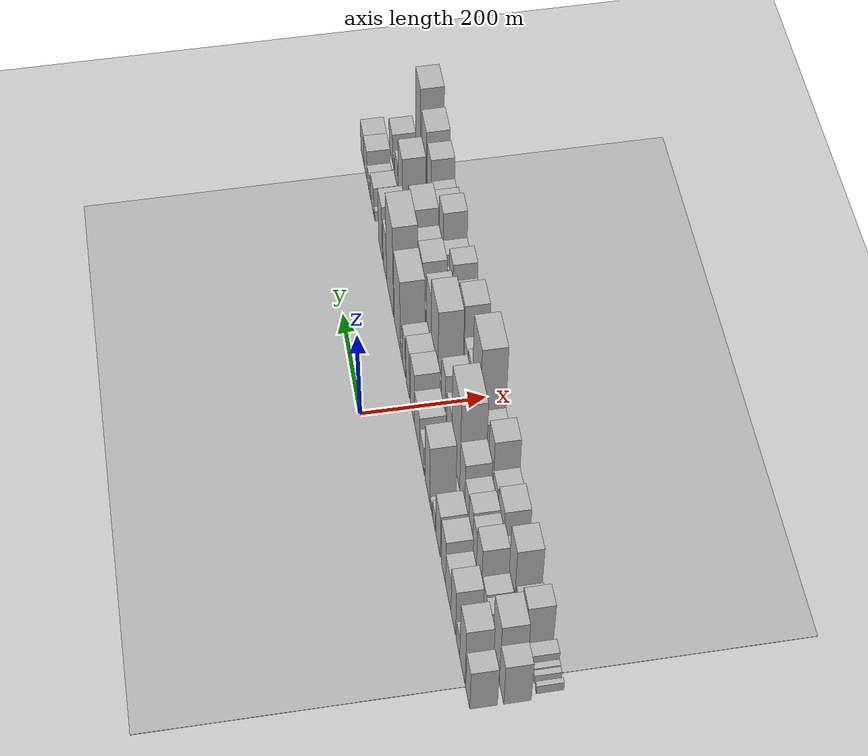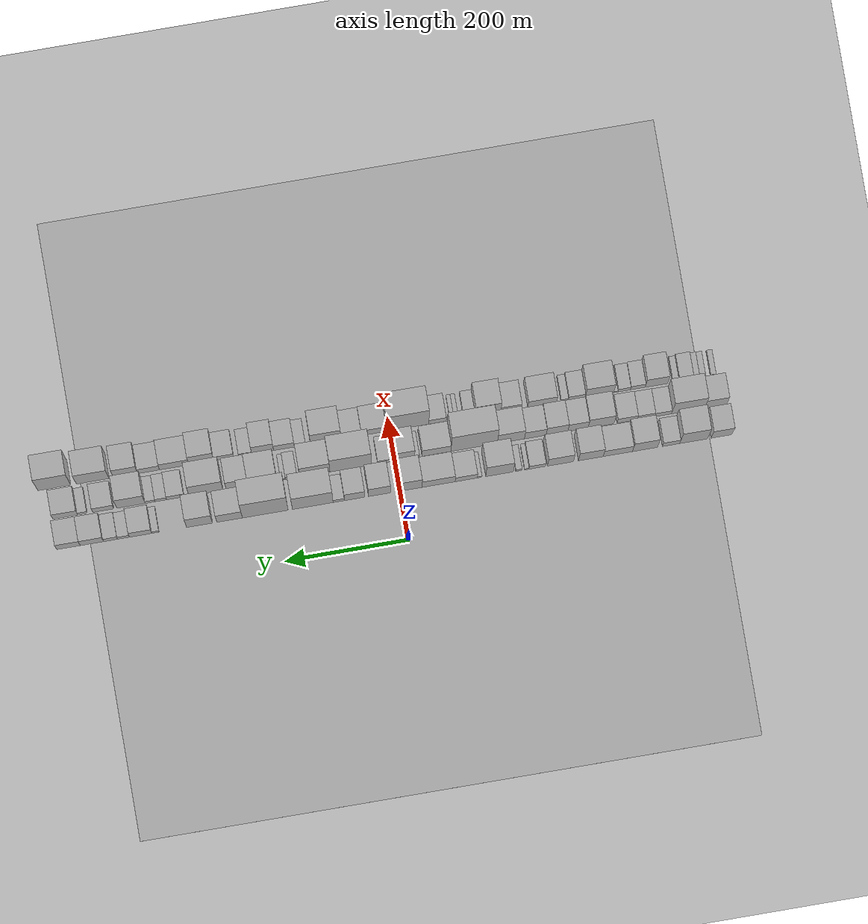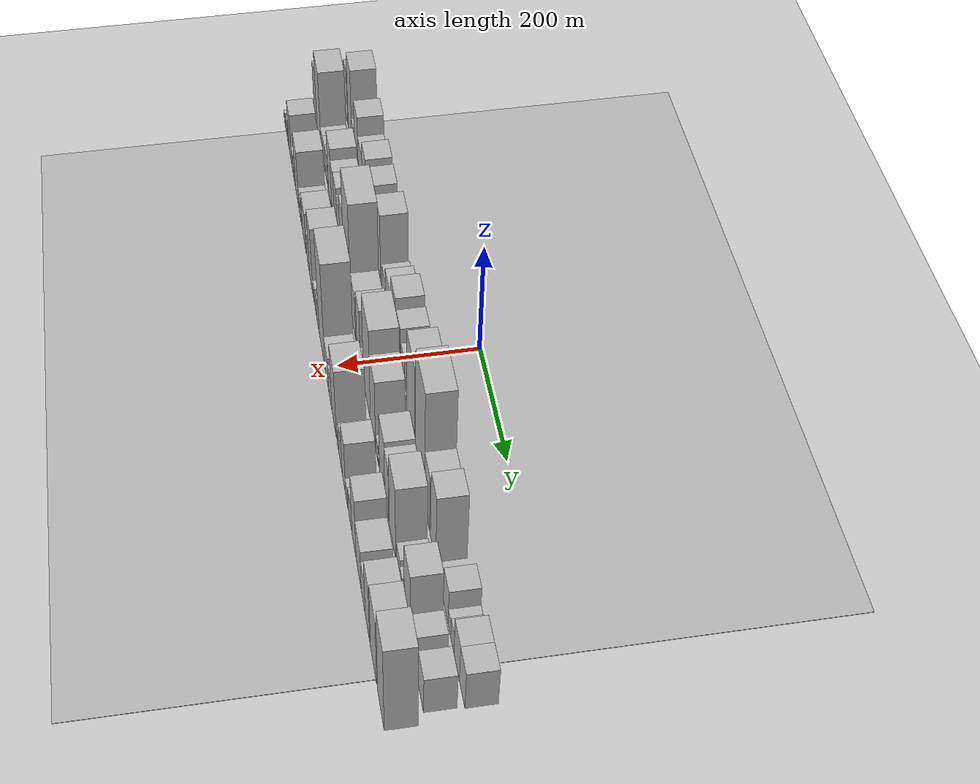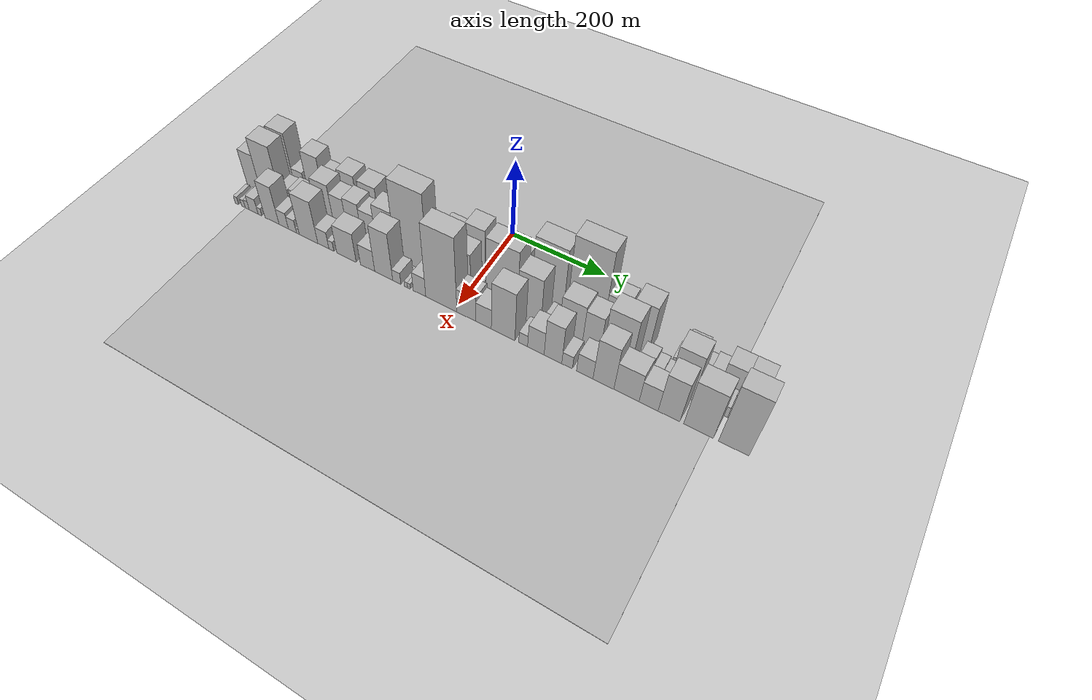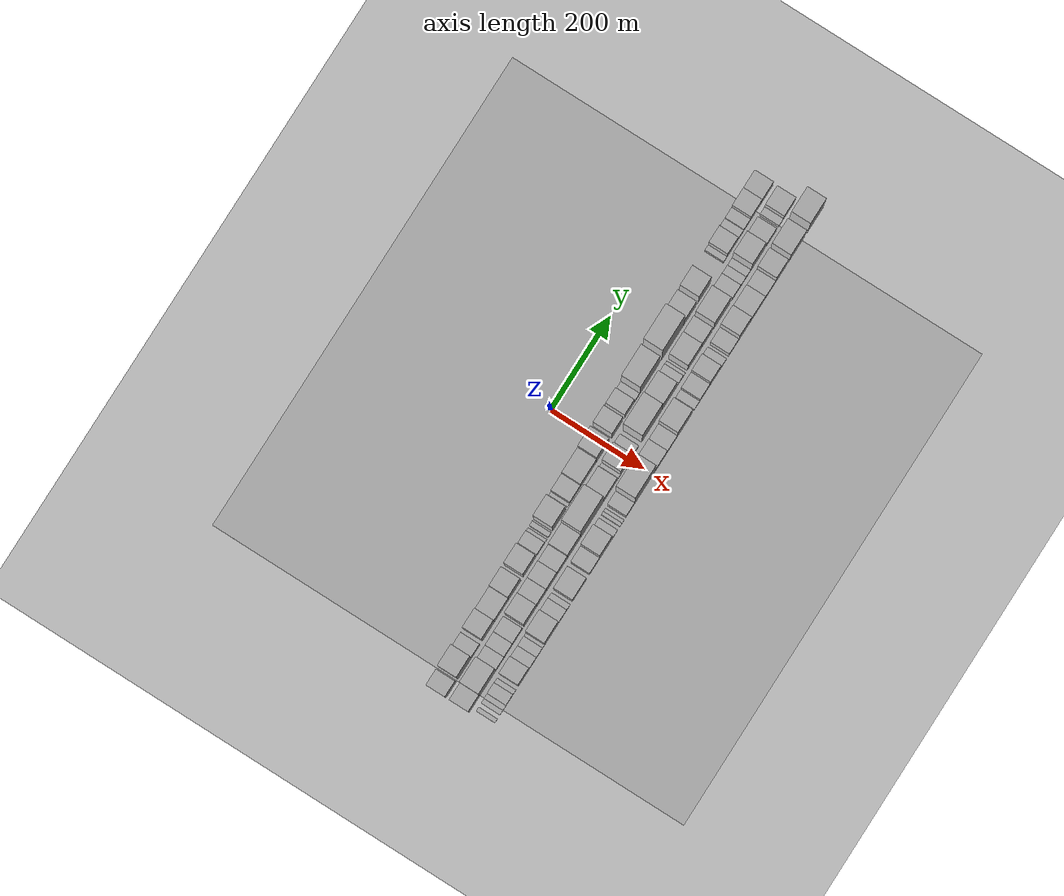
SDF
<?xml version="1.0" encoding="utf-8"?>

<sdf version="1.6">

   <world name="default">

      <gui fullscreen="0">

         <camera name="user_camera">

            <pose>-15 0 4.57585 0 0 0</pose>

            <view_controller>orbit</view_controller>

         </camera>

      </gui>

      <scene>

         <sky>

           <clouds>

             <speed>12</speed>

           </clouds>

         </sky>

         <ambient>0.4 0.4 0.4 1</ambient>

         <background>0.7 0.7 0.7 1</background>

         <shadows>1</shadows>

      </scene>

      <gravity>0 0 -9.8066</gravity>

      <magnetic_field>6e-06 2.3e-05 -4.2e-05</magnetic_field>

      <physics default="0" name="default_physics" type="ode">

         <ode>

            <solver>

               <type>quick</type>

               <iters>10</iters>

               <sor>1.0</sor>

               <use_dynamic_moi_rescaling>0</use_dynamic_moi_rescaling>

            </solver>

            <constraints>

               <cfm>0</cfm>

               <erp>0.2</erp>

               <contact_max_correcting_vel>100</contact_max_correcting_vel>

               <contact_surface_layer>0.001</contact_surface_layer>

            </constraints>

         </ode>

         <max_step_size>0.004</max_step_size>

         <real_time_factor>1</real_time_factor>

         <real_time_update_rate>250</real_time_update_rate>

      </physics>

      <light name="sun" type="directional">

         <cast_shadows>1</cast_shadows>

         <pose>0 0 10 0 0 0</pose>

         <diffuse>0.8 0.8 0.8 1</diffuse>

         <specular>0.2 0.2 0.2 1</specular>

         <attenuation>

            <range>1000</range>

            <constant>0.9</constant>

            <linear>0.01</linear>

            <quadratic>0.001</quadratic>

         </attenuation>

         <direction>-0.5 0.1 -0.9</direction>

      </light>

      <include>

         <name>ground_plane_1</name>

         <uri>model://HANNAS_ground_plane</uri>

         <pose>0 0 0  0 0 0</pose>

      </include>

      <include>

         <name>ground_plane_2</name>

         <uri>model://HANNAS_ground_plane</uri>

         <pose>100 0 0  0 0 0</pose>

      </include>

      <model name="building_1">

         <static>1</static>

         <pose frame="">100.0000 -519.1767 0 0.000000 0.000000 0.000000</pose>

         <link name="link">

            <pose frame="">0 0 51.00 0 0 0</pose>

            <collision name="collision">

               <geometry>

                  <box>

                     <size>40.0000 33.6465 102.0000</size>

                  </box>

               </geometry>

               <max_contacts>10</max_contacts>

               <surface>

                  <contact>

                     <ode/>

                  </contact>

                  <bounce/>

                  <friction>

                     <torsional>

                        <ode/>

                     </torsional>

                     <ode/>

                  </friction>

               </surface>

            </collision>

            <visual name="visual">

               <cast_shadows>0</cast_shadows>

               <geometry>

                  <box>

                     <size>40.0000 33.6465 102.0000</size>

                  </box>

               </geometry>

               <material>

                  <script>

                     <uri>model://HANNAS_wall/materials/scripts</uri>

                     <uri>model://HANNAS_wall/materials/textures</uri>

                     <name>vrc/HANNAS_wall</name>

                  </script>

               </material>

            </visual>

            <self_collide>0</self_collide>

            <enable_wind>0</enable_wind>

            <kinematic>0</kinematic>

         </link>

      </model>

      <model name="building_2">

         <static>1</static>

         <pose frame="">100.0000 -473.9205 0 0.000000 0.000000 0.000000</pose>

         <link name="link">

            <pose frame="">0 0 73.50 0 0 0</pose>

            <collision name="collision">

               <geometry>

                  <box>

                     <size>40.0000 44.8659 147.0000</size>

                  </box>

               </geometry>

               <max_contacts>10</max_contacts>

               <surface>

                  <contact>

                     <ode/>

                  </contact>

                  <bounce/>

                  <friction>

                     <torsional>

                        <ode/>

                     </torsional>

                     <ode/>

                  </friction>

               </surface>

            </collision>

            <visual name="visual">

               <cast_shadows>0</cast_shadows>

               <geometry>

                  <box>

                     <size>40.0000 44.8659 147.0000</size>

                  </box>

               </geometry>

               <material>

                  <script>

                     <uri>model://HANNAS_wall/materials/scripts</uri>

                     <uri>model://HANNAS_wall/materials/textures</uri>

                     <name>vrc/HANNAS_wall</name>

                  </script>

               </material>

            </visual>

            <self_collide>0</self_collide>

            <enable_wind>0</enable_wind>

            <kinematic>0</kinematic>

         </link>

      </model>

      <model name="building_3">

         <static>1</static>

         <pose frame="">100.0000 -437.5152 0 0.000000 0.000000 0.000000</pose>

         <link name="link">

            <pose frame="">0 0 27.00 0 0 0</pose>

            <collision name="collision">

               <geometry>

                  <box>

                     <size>40.0000 27.9448 54.0000</size>

                  </box>

               </geometry>

               <max_contacts>10</max_contacts>

               <surface>

                  <contact>

                     <ode/>

                  </contact>

                  <bounce/>

                  <friction>

                     <torsional>

                        <ode/>

                     </torsional>

                     <ode/>

                  </friction>

               </surface>

            </collision>

            <visual name="visual">

               <cast_shadows>0</cast_shadows>

               <geometry>

                  <box>

                     <size>40.0000 27.9448 54.0000</size>

                  </box>

               </geometry>

               <material>

                  <script>

                     <uri>model://HANNAS_wall/materials/scripts</uri>

                     <uri>model://HANNAS_wall/materials/textures</uri>

                     <name>vrc/HANNAS_wall</name>

                  </script>

               </material>

            </visual>

            <self_collide>0</self_collide>

            <enable_wind>0</enable_wind>

            <kinematic>0</kinematic>

         </link>

      </model>

      <model name="building_4">

         <static>1</static>

         <pose frame="">100.0000 -395.3650 0 0.000000 0.000000 0.000000</pose>

         <link name="link">

            <pose frame="">0 0 60.00 0 0 0</pose>

            <collision name="collision">

               <geometry>

                  <box>

                     <size>40.0000 40.3557 120.0000</size>

                  </box>

               </geometry>

               <max_contacts>10</max_contacts>

               <surface>

                  <contact>

                     <ode/>

                  </contact>

                  <bounce/>

                  <friction>

                     <torsional>

                        <ode/>

                     </torsional>

                     <ode/>

                  </friction>

               </surface>

            </collision>

            <visual name="visual">

               <cast_shadows>0</cast_shadows>

               <geometry>

                  <box>

                     <size>40.0000 40.3557 120.0000</size>

                  </box>

               </geometry>

               <material>

                  <script>

                     <uri>model://HANNAS_wall/materials/scripts</uri>

                     <uri>model://HANNAS_wall/materials/textures</uri>

                     <name>vrc/HANNAS_wall</name>

                  </script>

               </material>

            </visual>

            <self_collide>0</self_collide>

            <enable_wind>0</enable_wind>

            <kinematic>0</kinematic>

         </link>

      </model>

      <model name="building_5">

         <static>1</static>

         <pose frame="">100.0000 -351.5707 0 0.000000 0.000000 0.000000</pose>

         <link name="link">

            <pose frame="">0 0 42.00 0 0 0</pose>

            <collision name="collision">

               <geometry>

                  <box>

                     <size>40.0000 47.2327 84.0000</size>

                  </box>

               </geometry>

               <max_contacts>10</max_contacts>

               <surface>

                  <contact>

                     <ode/>

                  </contact>

                  <bounce/>

                  <friction>

                     <torsional>

                        <ode/>

                     </torsional>

                     <ode/>

                  </friction>

               </surface>

            </collision>

            <visual name="visual">

               <cast_shadows>0</cast_shadows>

               <geometry>

                  <box>

                     <size>40.0000 47.2327 84.0000</size>

                  </box>

               </geometry>

               <material>

                  <script>

                     <uri>model://HANNAS_wall/materials/scripts</uri>

                     <uri>model://HANNAS_wall/materials/textures</uri>

                     <name>vrc/HANNAS_wall</name>

                  </script>

               </material>

            </visual>

            <self_collide>0</self_collide>

            <enable_wind>0</enable_wind>

            <kinematic>0</kinematic>

         </link>

      </model>

      <model name="building_6">

         <static>1</static>

         <pose frame="">100.0000 -307.8718 0 0.000000 0.000000 0.000000</pose>

         <link name="link">

            <pose frame="">0 0 57.00 0 0 0</pose>

            <collision name="collision">

               <geometry>

                  <box>

                     <size>40.0000 40.1651 114.0000</size>

                  </box>

               </geometry>

               <max_contacts>10</max_contacts>

               <surface>

                  <contact>

                     <ode/>

                  </contact>

                  <bounce/>

                  <friction>

                     <torsional>

                        <ode/>

                     </torsional>

                     <ode/>

                  </friction>

               </surface>

            </collision>

            <visual name="visual">

               <cast_shadows>0</cast_shadows>

               <geometry>

                  <box>

                     <size>40.0000 40.1651 114.0000</size>

                  </box>

               </geometry>

               <material>

                  <script>

                     <uri>model://HANNAS_wall/materials/scripts</uri>

                     <uri>model://HANNAS_wall/materials/textures</uri>

                     <name>vrc/HANNAS_wall</name>

                  </script>

               </material>

            </visual>

            <self_collide>0</self_collide>

            <enable_wind>0</enable_wind>

            <kinematic>0</kinematic>

         </link>

      </model>

      <model name="building_7">

         <static>1</static>

         <pose frame="">100.0000 -258.7909 0 0.000000 0.000000 0.000000</pose>

         <link name="link">

            <pose frame="">0 0 54.00 0 0 0</pose>

            <collision name="collision">

               <geometry>

                  <box>

                     <size>40.0000 41.9967 108.0000</size>

                  </box>

               </geometry>

               <max_contacts>10</max_contacts>

               <surface>

                  <contact>

                     <ode/>

                  </contact>

                  <bounce/>

                  <friction>

                     <torsional>

                        <ode/>

                     </torsional>

                     <ode/>

                  </friction>

               </surface>

            </collision>

            <visual name="visual">

               <cast_shadows>0</cast_shadows>

               <geometry>

                  <box>

                     <size>40.0000 41.9967 108.0000</size>

                  </box>

               </geometry>

               <material>

                  <script>

                     <uri>model://HANNAS_wall/materials/scripts</uri>

                     <uri>model://HANNAS_wall/materials/textures</uri>

                     <name>vrc/HANNAS_wall</name>

                  </script>

               </material>

            </visual>

            <self_collide>0</self_collide>

            <enable_wind>0</enable_wind>

            <kinematic>0</kinematic>

         </link>

      </model>

      <model name="building_8">

         <static>1</static>

         <pose frame="">100.0000 -221.3957 0 0.000000 0.000000 0.000000</pose>

         <link name="link">

            <pose frame="">0 0 22.50 0 0 0</pose>

            <collision name="collision">

               <geometry>

                  <box>

                     <size>40.0000 26.7937 45.0000</size>

                  </box>

               </geometry>

               <max_contacts>10</max_contacts>

               <surface>

                  <contact>

                     <ode/>

                  </contact>

                  <bounce/>

                  <friction>

                     <torsional>

                        <ode/>

                     </torsional>

                     <ode/>

                  </friction>

               </surface>

            </collision>

            <visual name="visual">

               <cast_shadows>0</cast_shadows>

               <geometry>

                  <box>

                     <size>40.0000 26.7937 45.0000</size>

                  </box>

               </geometry>

               <material>

                  <script>

                     <uri>model://HANNAS_wall/materials/scripts</uri>

                     <uri>model://HANNAS_wall/materials/textures</uri>

                     <name>vrc/HANNAS_wall</name>

                  </script>

               </material>

            </visual>

            <self_collide>0</self_collide>

            <enable_wind>0</enable_wind>

            <kinematic>0</kinematic>

         </link>

      </model>

      <model name="building_9">

         <static>1</static>

         <pose frame="">100.0000 -204.3050 0 0.000000 0.000000 0.000000</pose>

         <link name="link">

            <pose frame="">0 0 9.00 0 0 0</pose>

            <collision name="collision">

               <geometry>

                  <box>

                     <size>40.0000 7.3877 18.0000</size>

                  </box>

               </geometry>

               <max_contacts>10</max_contacts>

               <surface>

                  <contact>

                     <ode/>

                  </contact>

                  <bounce/>

                  <friction>

                     <torsional>

                        <ode/>

                     </torsional>

                     <ode/>

                  </friction>

               </surface>

            </collision>

            <visual name="visual">

               <cast_shadows>0</cast_shadows>

               <geometry>

                  <box>

                     <size>40.0000 7.3877 18.0000</size>

                  </box>

               </geometry>

               <material>

                  <script>

                     <uri>model://HANNAS_wall/materials/scripts</uri>

                     <uri>model://HANNAS_wall/materials/textures</uri>

                     <name>vrc/HANNAS_wall</name>

                  </script>

               </material>

            </visual>

            <self_collide>0</self_collide>

            <enable_wind>0</enable_wind>

            <kinematic>0</kinematic>

         </link>

      </model>

      <model name="building_10">

         <static>1</static>

         <pose frame="">100.0000 -191.5914 0 0.000000 0.000000 0.000000</pose>

         <link name="link">

            <pose frame="">0 0 12.00 0 0 0</pose>

            <collision name="collision">

               <geometry>

                  <box>

                     <size>40.0000 10.0394 24.0000</size>

                  </box>

               </geometry>

               <max_contacts>10</max_contacts>

               <surface>

                  <contact>

                     <ode/>

                  </contact>

                  <bounce/>

                  <friction>

                     <torsional>

                        <ode/>

                     </torsional>

                     <ode/>

                  </friction>

               </surface>

            </collision>

            <visual name="visual">

               <cast_shadows>0</cast_shadows>

               <geometry>

                  <box>

                     <size>40.0000 10.0394 24.0000</size>

                  </box>

               </geometry>

               <material>

                  <script>

                     <uri>model://HANNAS_wall/materials/scripts</uri>

                     <uri>model://HANNAS_wall/materials/textures</uri>

                     <name>vrc/HANNAS_wall</name>

                  </script>

               </material>

            </visual>

            <self_collide>0</self_collide>

            <enable_wind>0</enable_wind>

            <kinematic>0</kinematic>

         </link>

      </model>

      <model name="building_11">

         <static>1</static>

         <pose frame="">100.0000 -160.2970 0 0.000000 0.000000 0.000000</pose>

         <link name="link">

            <pose frame="">0 0 72.00 0 0 0</pose>

            <collision name="collision">

               <geometry>

                  <box>

                     <size>40.0000 44.5494 144.0000</size>

                  </box>

               </geometry>

               <max_contacts>10</max_contacts>

               <surface>

                  <contact>

                     <ode/>

                  </contact>

                  <bounce/>

                  <friction>

                     <torsional>

                        <ode/>

                     </torsional>

                     <ode/>

                  </friction>

               </surface>

            </collision>

            <visual name="visual">

               <cast_shadows>0</cast_shadows>

               <geometry>

                  <box>

                     <size>40.0000 44.5494 144.0000</size>

                  </box>

               </geometry>

               <material>

                  <script>

                     <uri>model://HANNAS_wall/materials/scripts</uri>

                     <uri>model://HANNAS_wall/materials/textures</uri>

                     <name>vrc/HANNAS_wall</name>

                  </script>

               </material>

            </visual>

            <self_collide>0</self_collide>

            <enable_wind>0</enable_wind>

            <kinematic>0</kinematic>

         </link>

      </model>

      <model name="building_12">

         <static>1</static>

         <pose frame="">100.0000 -128.2842 0 0.000000 0.000000 0.000000</pose>

         <link name="link">

            <pose frame="">0 0 9.00 0 0 0</pose>

            <collision name="collision">

               <geometry>

                  <box>

                     <size>40.0000 7.4762 18.0000</size>

                  </box>

               </geometry>

               <max_contacts>10</max_contacts>

               <surface>

                  <contact>

                     <ode/>

                  </contact>

                  <bounce/>

                  <friction>

                     <torsional>

                        <ode/>

                     </torsional>

                     <ode/>

                  </friction>

               </surface>

            </collision>

            <visual name="visual">

               <cast_shadows>0</cast_shadows>

               <geometry>

                  <box>

                     <size>40.0000 7.4762 18.0000</size>

                  </box>

               </geometry>

               <material>

                  <script>

                     <uri>model://HANNAS_wall/materials/scripts</uri>

                     <uri>model://HANNAS_wall/materials/textures</uri>

                     <name>vrc/HANNAS_wall</name>

                  </script>

               </material>

            </visual>

            <self_collide>0</self_collide>

            <enable_wind>0</enable_wind>

            <kinematic>0</kinematic>

         </link>

      </model>

      <model name="building_13">

         <static>1</static>

         <pose frame="">100.0000 -106.5795 0 0.000000 0.000000 0.000000</pose>

         <link name="link">

            <pose frame="">0 0 31.50 0 0 0</pose>

            <collision name="collision">

               <geometry>

                  <box>

                     <size>40.0000 35.9331 63.0000</size>

                  </box>

               </geometry>

               <max_contacts>10</max_contacts>

               <surface>

                  <contact>

                     <ode/>

                  </contact>

                  <bounce/>

                  <friction>

                     <torsional>

                        <ode/>

                     </torsional>

                     <ode/>

                  </friction>

               </surface>

            </collision>

            <visual name="visual">

               <cast_shadows>0</cast_shadows>

               <geometry>

                  <box>

                     <size>40.0000 35.9331 63.0000</size>

                  </box>

               </geometry>

               <material>

                  <script>

                     <uri>model://HANNAS_wall/materials/scripts</uri>

                     <uri>model://HANNAS_wall/materials/textures</uri>

                     <name>vrc/HANNAS_wall</name>

                  </script>

               </material>

            </visual>

            <self_collide>0</self_collide>

            <enable_wind>0</enable_wind>

            <kinematic>0</kinematic>

         </link>

      </model>

      <model name="building_14">

         <static>1</static>

         <pose frame="">100.0000 -61.9898 0 0.000000 0.000000 0.000000</pose>

         <link name="link">

            <pose frame="">0 0 45.00 0 0 0</pose>

            <collision name="collision">

               <geometry>

                  <box>

                     <size>40.0000 53.2462 90.0000</size>

                  </box>

               </geometry>

               <max_contacts>10</max_contacts>

               <surface>

                  <contact>

                     <ode/>

                  </contact>

                  <bounce/>

                  <friction>

                     <torsional>

                        <ode/>

                     </torsional>

                     <ode/>

                  </friction>

               </surface>

            </collision>

            <visual name="visual">

               <cast_shadows>0</cast_shadows>

               <geometry>

                  <box>

                     <size>40.0000 53.2462 90.0000</size>

                  </box>

               </geometry>

               <material>

                  <script>

                     <uri>model://HANNAS_wall/materials/scripts</uri>

                     <uri>model://HANNAS_wall/materials/textures</uri>

                     <name>vrc/HANNAS_wall</name>

                  </script>

               </material>

            </visual>

            <self_collide>0</self_collide>

            <enable_wind>0</enable_wind>

            <kinematic>0</kinematic>

         </link>

      </model>

      <model name="building_15">

         <static>1</static>

         <pose frame="">100.0000 -14.3480 0 0.000000 0.000000 0.000000</pose>

         <link name="link">

            <pose frame="">0 0 64.50 0 0 0</pose>

            <collision name="collision">

               <geometry>

                  <box>

                     <size>40.0000 42.0374 129.0000</size>

                  </box>

               </geometry>

               <max_contacts>10</max_contacts>

               <surface>

                  <contact>

                     <ode/>

                  </contact>

                  <bounce/>

                  <friction>

                     <torsional>

                        <ode/>

                     </torsional>

                     <ode/>

                  </friction>

               </surface>

            </collision>

            <visual name="visual">

               <cast_shadows>0</cast_shadows>

               <geometry>

                  <box>

                     <size>40.0000 42.0374 129.0000</size>

                  </box>

               </geometry>

               <material>

                  <script>

                     <uri>model://HANNAS_wall/materials/scripts</uri>

                     <uri>model://HANNAS_wall/materials/textures</uri>

                     <name>vrc/HANNAS_wall</name>

                  </script>

               </material>

            </visual>

            <self_collide>0</self_collide>

            <enable_wind>0</enable_wind>

            <kinematic>0</kinematic>

         </link>

      </model>

      <model name="building_16">

         <static>1</static>

         <pose frame="">100.0000 33.4773 0 0.000000 0.000000 0.000000</pose>

         <link name="link">

            <pose frame="">0 0 58.50 0 0 0</pose>

            <collision name="collision">

               <geometry>

                  <box>

                     <size>40.0000 35.6132 117.0000</size>

                  </box>

               </geometry>

               <max_contacts>10</max_contacts>

               <surface>

                  <contact>

                     <ode/>

                  </contact>

                  <bounce/>

                  <friction>

                     <torsional>

                        <ode/>

                     </torsional>

                     <ode/>

                  </friction>

               </surface>

            </collision>

            <visual name="visual">

               <cast_shadows>0</cast_shadows>

               <geometry>

                  <box>

                     <size>40.0000 35.6132 117.0000</size>

                  </box>

               </geometry>

               <material>

                  <script>

                     <uri>model://HANNAS_wall/materials/scripts</uri>

                     <uri>model://HANNAS_wall/materials/textures</uri>

                     <name>vrc/HANNAS_wall</name>

                  </script>

               </material>

            </visual>

            <self_collide>0</self_collide>

            <enable_wind>0</enable_wind>

            <kinematic>0</kinematic>

         </link>

      </model>

      <model name="building_17">

         <static>1</static>

         <pose frame="">100.0000 73.7126 0 0.000000 0.000000 0.000000</pose>

         <link name="link">

            <pose frame="">0 0 48.00 0 0 0</pose>

            <collision name="collision">

               <geometry>

                  <box>

                     <size>40.0000 32.8575 96.0000</size>

                  </box>

               </geometry>

               <max_contacts>10</max_contacts>

               <surface>

                  <contact>

                     <ode/>

                  </contact>

                  <bounce/>

                  <friction>

                     <torsional>

                        <ode/>

                     </torsional>

                     <ode/>

                  </friction>

               </surface>

            </collision>

            <visual name="visual">

               <cast_shadows>0</cast_shadows>

               <geometry>

                  <box>

                     <size>40.0000 32.8575 96.0000</size>

                  </box>

               </geometry>

               <material>

                  <script>

                     <uri>model://HANNAS_wall/materials/scripts</uri>

                     <uri>model://HANNAS_wall/materials/textures</uri>

                     <name>vrc/HANNAS_wall</name>

                  </script>

               </material>

            </visual>

            <self_collide>0</self_collide>

            <enable_wind>0</enable_wind>

            <kinematic>0</kinematic>

         </link>

      </model>

      <model name="building_18">

         <static>1</static>

         <pose frame="">100.0000 99.3036 0 0.000000 0.000000 0.000000</pose>

         <link name="link">

            <pose frame="">0 0 18.00 0 0 0</pose>

            <collision name="collision">

               <geometry>

                  <box>

                     <size>40.0000 18.3245 36.0000</size>

                  </box>

               </geometry>

               <max_contacts>10</max_contacts>

               <surface>

                  <contact>

                     <ode/>

                  </contact>

                  <bounce/>

                  <friction>

                     <torsional>

                        <ode/>

                     </torsional>

                     <ode/>

                  </friction>

               </surface>

            </collision>

            <visual name="visual">

               <cast_shadows>0</cast_shadows>

               <geometry>

                  <box>

                     <size>40.0000 18.3245 36.0000</size>

                  </box>

               </geometry>

               <material>

                  <script>

                     <uri>model://HANNAS_wall/materials/scripts</uri>

                     <uri>model://HANNAS_wall/materials/textures</uri>

                     <name>vrc/HANNAS_wall</name>

                  </script>

               </material>

            </visual>

            <self_collide>0</self_collide>

            <enable_wind>0</enable_wind>

            <kinematic>0</kinematic>

         </link>

      </model>

      <model name="building_19">

         <static>1</static>

         <pose frame="">100.0000 141.2515 0 0.000000 0.000000 0.000000</pose>

         <link name="link">

            <pose frame="">0 0 88.50 0 0 0</pose>

            <collision name="collision">

               <geometry>

                  <box>

                     <size>40.0000 65.5714 177.0000</size>

                  </box>

               </geometry>

               <max_contacts>10</max_contacts>

               <surface>

                  <contact>

                     <ode/>

                  </contact>

                  <bounce/>

                  <friction>

                     <torsional>

                        <ode/>

                     </torsional>

                     <ode/>

                  </friction>

               </surface>

            </collision>

            <visual name="visual">

               <cast_shadows>0</cast_shadows>

               <geometry>

                  <box>

                     <size>40.0000 65.5714 177.0000</size>

                  </box>

               </geometry>

               <material>

                  <script>

                     <uri>model://HANNAS_wall/materials/scripts</uri>

                     <uri>model://HANNAS_wall/materials/textures</uri>

                     <name>vrc/HANNAS_wall</name>

                  </script>

               </material>

            </visual>

            <self_collide>0</self_collide>

            <enable_wind>0</enable_wind>

            <kinematic>0</kinematic>

         </link>

      </model>

      <model name="building_20">

         <static>1</static>

         <pose frame="">100.0000 217.8878 0 0.000000 0.000000 0.000000</pose>

         <link name="link">

            <pose frame="">0 0 111.00 0 0 0</pose>

            <collision name="collision">

               <geometry>

                  <box>

                     <size>40.0000 73.7011 222.0000</size>

                  </box>

               </geometry>

               <max_contacts>10</max_contacts>

               <surface>

                  <contact>

                     <ode/>

                  </contact>

                  <bounce/>

                  <friction>

                     <torsional>

                        <ode/>

                     </torsional>

                     <ode/>

                  </friction>

               </surface>

            </collision>

            <visual name="visual">

               <cast_shadows>0</cast_shadows>

               <geometry>

                  <box>

                     <size>40.0000 73.7011 222.0000</size>

                  </box>

               </geometry>

               <material>

                  <script>

                     <uri>model://HANNAS_wall/materials/scripts</uri>

                     <uri>model://HANNAS_wall/materials/textures</uri>

                     <name>vrc/HANNAS_wall</name>

                  </script>

               </material>

            </visual>

            <self_collide>0</self_collide>

            <enable_wind>0</enable_wind>

            <kinematic>0</kinematic>

         </link>

      </model>

      <model name="building_21">

         <static>1</static>

         <pose frame="">100.0000 275.3792 0 0.000000 0.000000 0.000000</pose>

         <link name="link">

            <pose frame="">0 0 55.50 0 0 0</pose>

            <collision name="collision">

               <geometry>

                  <box>

                     <size>40.0000 41.2819 111.0000</size>

                  </box>

               </geometry>

               <max_contacts>10</max_contacts>

               <surface>

                  <contact>

                     <ode/>

                  </contact>

                  <bounce/>

                  <friction>

                     <torsional>

                        <ode/>

                     </torsional>

                     <ode/>

                  </friction>

               </surface>

            </collision>

            <visual name="visual">

               <cast_shadows>0</cast_shadows>

               <geometry>

                  <box>

                     <size>40.0000 41.2819 111.0000</size>

                  </box>

               </geometry>

               <material>

                  <script>

                     <uri>model://HANNAS_wall/materials/scripts</uri>

                     <uri>model://HANNAS_wall/materials/textures</uri>

                     <name>vrc/HANNAS_wall</name>

                  </script>

               </material>

            </visual>

            <self_collide>0</self_collide>

            <enable_wind>0</enable_wind>

            <kinematic>0</kinematic>

         </link>

      </model>

      <model name="building_22">

         <static>1</static>

         <pose frame="">100.0000 323.8332 0 0.000000 0.000000 0.000000</pose>

         <link name="link">

            <pose frame="">0 0 66.00 0 0 0</pose>

            <collision name="collision">

               <geometry>

                  <box>

                     <size>40.0000 41.6261 132.0000</size>

                  </box>

               </geometry>

               <max_contacts>10</max_contacts>

               <surface>

                  <contact>

                     <ode/>

                  </contact>

                  <bounce/>

                  <friction>

                     <torsional>

                        <ode/>

                     </torsional>

                     <ode/>

                  </friction>

               </surface>

            </collision>

            <visual name="visual">

               <cast_shadows>0</cast_shadows>

               <geometry>

                  <box>

                     <size>40.0000 41.6261 132.0000</size>

                  </box>

               </geometry>

               <material>

                  <script>

                     <uri>model://HANNAS_wall/materials/scripts</uri>

                     <uri>model://HANNAS_wall/materials/textures</uri>

                     <name>vrc/HANNAS_wall</name>

                  </script>

               </material>

            </visual>

            <self_collide>0</self_collide>

            <enable_wind>0</enable_wind>

            <kinematic>0</kinematic>

         </link>

      </model>

      <model name="building_23">

         <static>1</static>

         <pose frame="">100.0000 394.9976 0 0.000000 0.000000 0.000000</pose>

         <link name="link">

            <pose frame="">0 0 12.00 0 0 0</pose>

            <collision name="collision">

               <geometry>

                  <box>

                     <size>40.0000 11.5676 24.0000</size>

                  </box>

               </geometry>

               <max_contacts>10</max_contacts>

               <surface>

                  <contact>

                     <ode/>

                  </contact>

                  <bounce/>

                  <friction>

                     <torsional>

                        <ode/>

                     </torsional>

                     <ode/>

                  </friction>

               </surface>

            </collision>

            <visual name="visual">

               <cast_shadows>0</cast_shadows>

               <geometry>

                  <box>

                     <size>40.0000 11.5676 24.0000</size>

                  </box>

               </geometry>

               <material>

                  <script>

                     <uri>model://HANNAS_wall/materials/scripts</uri>

                     <uri>model://HANNAS_wall/materials/textures</uri>

                     <name>vrc/HANNAS_wall</name>

                  </script>

               </material>

            </visual>

            <self_collide>0</self_collide>

            <enable_wind>0</enable_wind>

            <kinematic>0</kinematic>

         </link>

      </model>

      <model name="building_24">

         <static>1</static>

         <pose frame="">100.0000 418.7170 0 0.000000 0.000000 0.000000</pose>

         <link name="link">

            <pose frame="">0 0 34.50 0 0 0</pose>

            <collision name="collision">

               <geometry>

                  <box>

                     <size>40.0000 35.8713 69.0000</size>

                  </box>

               </geometry>

               <max_contacts>10</max_contacts>

               <surface>

                  <contact>

                     <ode/>

                  </contact>

                  <bounce/>

                  <friction>

                     <torsional>

                        <ode/>

                     </torsional>

                     <ode/>

                  </friction>

               </surface>

            </collision>

            <visual name="visual">

               <cast_shadows>0</cast_shadows>

               <geometry>

                  <box>

                     <size>40.0000 35.8713 69.0000</size>

                  </box>

               </geometry>

               <material>

                  <script>

                     <uri>model://HANNAS_wall/materials/scripts</uri>

                     <uri>model://HANNAS_wall/materials/textures</uri>

                     <name>vrc/HANNAS_wall</name>

                  </script>

               </material>

            </visual>

            <self_collide>0</self_collide>

            <enable_wind>0</enable_wind>

            <kinematic>0</kinematic>

         </link>

      </model>

      <model name="building_25">

         <static>1</static>

         <pose frame="">100.0000 446.3657 0 0.000000 0.000000 0.000000</pose>

         <link name="link">

            <pose frame="">0 0 16.50 0 0 0</pose>

            <collision name="collision">

               <geometry>

                  <box>

                     <size>40.0000 19.4260 33.0000</size>

                  </box>

               </geometry>

               <max_contacts>10</max_contacts>

               <surface>

                  <contact>

                     <ode/>

                  </contact>

                  <bounce/>

                  <friction>

                     <torsional>

                        <ode/>

                     </torsional>

                     <ode/>

                  </friction>

               </surface>

            </collision>

            <visual name="visual">

               <cast_shadows>0</cast_shadows>

               <geometry>

                  <box>

                     <size>40.0000 19.4260 33.0000</size>

                  </box>

               </geometry>

               <material>

                  <script>

                     <uri>model://HANNAS_wall/materials/scripts</uri>

                     <uri>model://HANNAS_wall/materials/textures</uri>

                     <name>vrc/HANNAS_wall</name>

                  </script>

               </material>

            </visual>

            <self_collide>0</self_collide>

            <enable_wind>0</enable_wind>

            <kinematic>0</kinematic>

         </link>

      </model>

      <model name="building_26">

         <static>1</static>

         <pose frame="">100.0000 467.3186 0 0.000000 0.000000 0.000000</pose>

         <link name="link">

            <pose frame="">0 0 21.00 0 0 0</pose>

            <collision name="collision">

               <geometry>

                  <box>

                     <size>40.0000 22.4799 42.0000</size>

                  </box>

               </geometry>

               <max_contacts>10</max_contacts>

               <surface>

                  <contact>

                     <ode/>

                  </contact>

                  <bounce/>

                  <friction>

                     <torsional>

                        <ode/>

                     </torsional>

                     <ode/>

                  </friction>

               </surface>

            </collision>

            <visual name="visual">

               <cast_shadows>0</cast_shadows>

               <geometry>

                  <box>

                     <size>40.0000 22.4799 42.0000</size>

                  </box>

               </geometry>

               <material>

                  <script>

                     <uri>model://HANNAS_wall/materials/scripts</uri>

                     <uri>model://HANNAS_wall/materials/textures</uri>

                     <name>vrc/HANNAS_wall</name>

                  </script>

               </material>

            </visual>

            <self_collide>0</self_collide>

            <enable_wind>0</enable_wind>

            <kinematic>0</kinematic>

         </link>

      </model>

      <model name="building_27">

         <static>1</static>

         <pose frame="">100.0000 497.3956 0 0.000000 0.000000 0.000000</pose>

         <link name="link">

            <pose frame="">0 0 37.50 0 0 0</pose>

            <collision name="collision">

               <geometry>

                  <box>

                     <size>40.0000 37.6741 75.0000</size>

                  </box>

               </geometry>

               <max_contacts>10</max_contacts>

               <surface>

                  <contact>

                     <ode/>

                  </contact>

                  <bounce/>

                  <friction>

                     <torsional>

                        <ode/>

                     </torsional>

                     <ode/>

                  </friction>

               </surface>

            </collision>

            <visual name="visual">

               <cast_shadows>0</cast_shadows>

               <geometry>

                  <box>

                     <size>40.0000 37.6741 75.0000</size>

                  </box>

               </geometry>

               <material>

                  <script>

                     <uri>model://HANNAS_wall/materials/scripts</uri>

                     <uri>model://HANNAS_wall/materials/textures</uri>

                     <name>vrc/HANNAS_wall</name>

                  </script>

               </material>

            </visual>

            <self_collide>0</self_collide>

            <enable_wind>0</enable_wind>

            <kinematic>0</kinematic>

         </link>

      </model>

      <model name="building_28">

         <static>1</static>

         <pose frame="">100.0000 535.1315 0 0.000000 0.000000 0.000000</pose>

         <link name="link">

            <pose frame="">0 0 37.50 0 0 0</pose>

            <collision name="collision">

               <geometry>

                  <box>

                     <size>40.0000 37.7977 75.0000</size>

                  </box>

               </geometry>

               <max_contacts>10</max_contacts>

               <surface>

                  <contact>

                     <ode/>

                  </contact>

                  <bounce/>

                  <friction>

                     <torsional>

                        <ode/>

                     </torsional>

                     <ode/>

                  </friction>

               </surface>

            </collision>

            <visual name="visual">

               <cast_shadows>0</cast_shadows>

               <geometry>

                  <box>

                     <size>40.0000 37.7977 75.0000</size>

                  </box>

               </geometry>

               <material>

                  <script>

                     <uri>model://HANNAS_wall/materials/scripts</uri>

                     <uri>model://HANNAS_wall/materials/textures</uri>

                     <name>vrc/HANNAS_wall</name>

                  </script>

               </material>

            </visual>

            <self_collide>0</self_collide>

            <enable_wind>0</enable_wind>

            <kinematic>0</kinematic>

         </link>

      </model>

      <model name="building_29">

         <static>1</static>

         <pose frame="">149.0000 -518.1014 0 0.000000 0.000000 0.000000</pose>

         <link name="link">

            <pose frame="">0 0 52.50 0 0 0</pose>

            <collision name="collision">

               <geometry>

                  <box>

                     <size>40.0000 35.7971 105.0000</size>

                  </box>

               </geometry>

               <max_contacts>10</max_contacts>

               <surface>

                  <contact>

                     <ode/>

                  </contact>

                  <bounce/>

                  <friction>

                     <torsional>

                        <ode/>

                     </torsional>

                     <ode/>

                  </friction>

               </surface>

            </collision>

            <visual name="visual">

               <cast_shadows>0</cast_shadows>

               <geometry>

                  <box>

                     <size>40.0000 35.7971 105.0000</size>

                  </box>

               </geometry>

               <material>

                  <script>

                     <uri>model://HANNAS_wall/materials/scripts</uri>

                     <uri>model://HANNAS_wall/materials/textures</uri>

                     <name>vrc/HANNAS_wall</name>

                  </script>

               </material>

            </visual>

            <self_collide>0</self_collide>

            <enable_wind>0</enable_wind>

            <kinematic>0</kinematic>

         </link>

      </model>

      <model name="building_30">

         <static>1</static>

         <pose frame="">149.0000 -473.4842 0 0.000000 0.000000 0.000000</pose>

         <link name="link">

            <pose frame="">0 0 76.50 0 0 0</pose>

            <collision name="collision">

               <geometry>

                  <box>

                     <size>40.0000 53.4373 153.0000</size>

                  </box>

               </geometry>

               <max_contacts>10</max_contacts>

               <surface>

                  <contact>

                     <ode/>

                  </contact>

                  <bounce/>

                  <friction>

                     <torsional>

                        <ode/>

                     </torsional>

                     <ode/>

                  </friction>

               </surface>

            </collision>

            <visual name="visual">

               <cast_shadows>0</cast_shadows>

               <geometry>

                  <box>

                     <size>40.0000 53.4373 153.0000</size>

                  </box>

               </geometry>

               <material>

                  <script>

                     <uri>model://HANNAS_wall/materials/scripts</uri>

                     <uri>model://HANNAS_wall/materials/textures</uri>

                     <name>vrc/HANNAS_wall</name>

                  </script>

               </material>

            </visual>

            <self_collide>0</self_collide>

            <enable_wind>0</enable_wind>

            <kinematic>0</kinematic>

         </link>

      </model>

      <model name="building_31">

         <static>1</static>

         <pose frame="">149.0000 -433.1350 0 0.000000 0.000000 0.000000</pose>

         <link name="link">

            <pose frame="">0 0 24.00 0 0 0</pose>

            <collision name="collision">

               <geometry>

                  <box>

                     <size>40.0000 27.2611 48.0000</size>

                  </box>

               </geometry>

               <max_contacts>10</max_contacts>

               <surface>

                  <contact>

                     <ode/>

                  </contact>

                  <bounce/>

                  <friction>

                     <torsional>

                        <ode/>

                     </torsional>

                     <ode/>

                  </friction>

               </surface>

            </collision>

            <visual name="visual">

               <cast_shadows>0</cast_shadows>

               <geometry>

                  <box>

                     <size>40.0000 27.2611 48.0000</size>

                  </box>

               </geometry>

               <material>

                  <script>

                     <uri>model://HANNAS_wall/materials/scripts</uri>

                     <uri>model://HANNAS_wall/materials/textures</uri>

                     <name>vrc/HANNAS_wall</name>

                  </script>

               </material>

            </visual>

            <self_collide>0</self_collide>

            <enable_wind>0</enable_wind>

            <kinematic>0</kinematic>

         </link>

      </model>

      <model name="building_32">

         <static>1</static>

         <pose frame="">149.0000 -405.4768 0 0.000000 0.000000 0.000000</pose>

         <link name="link">

            <pose frame="">0 0 27.00 0 0 0</pose>

            <collision name="collision">

               <geometry>

                  <box>

                     <size>40.0000 28.0553 54.0000</size>

                  </box>

               </geometry>

               <max_contacts>10</max_contacts>

               <surface>

                  <contact>

                     <ode/>

                  </contact>

                  <bounce/>

                  <friction>

                     <torsional>

                        <ode/>

                     </torsional>

                     <ode/>

                  </friction>

               </surface>

            </collision>

            <visual name="visual">

               <cast_shadows>0</cast_shadows>

               <geometry>

                  <box>

                     <size>40.0000 28.0553 54.0000</size>

                  </box>

               </geometry>

               <material>

                  <script>

                     <uri>model://HANNAS_wall/materials/scripts</uri>

                     <uri>model://HANNAS_wall/materials/textures</uri>

                     <name>vrc/HANNAS_wall</name>

                  </script>

               </material>

            </visual>

            <self_collide>0</self_collide>

            <enable_wind>0</enable_wind>

            <kinematic>0</kinematic>

         </link>

      </model>

      <model name="building_33">

         <static>1</static>

         <pose frame="">149.0000 -375.0897 0 0.000000 0.000000 0.000000</pose>

         <link name="link">

            <pose frame="">0 0 30.00 0 0 0</pose>

            <collision name="collision">

               <geometry>

                  <box>

                     <size>40.0000 32.7190 60.0000</size>

                  </box>

               </geometry>

               <max_contacts>10</max_contacts>

               <surface>

                  <contact>

                     <ode/>

                  </contact>

                  <bounce/>

                  <friction>

                     <torsional>

                        <ode/>

                     </torsional>

                     <ode/>

                  </friction>

               </surface>

            </collision>

            <visual name="visual">

               <cast_shadows>0</cast_shadows>

               <geometry>

                  <box>

                     <size>40.0000 32.7190 60.0000</size>

                  </box>

               </geometry>

               <material>

                  <script>

                     <uri>model://HANNAS_wall/materials/scripts</uri>

                     <uri>model://HANNAS_wall/materials/textures</uri>

                     <name>vrc/HANNAS_wall</name>

                  </script>

               </material>

            </visual>

            <self_collide>0</self_collide>

            <enable_wind>0</enable_wind>

            <kinematic>0</kinematic>

         </link>

      </model>

      <model name="building_34">

         <static>1</static>

         <pose frame="">149.0000 -332.7473 0 0.000000 0.000000 0.000000</pose>

         <link name="link">

            <pose frame="">0 0 60.00 0 0 0</pose>

            <collision name="collision">

               <geometry>

                  <box>

                     <size>40.0000 41.9658 120.0000</size>

                  </box>

               </geometry>

               <max_contacts>10</max_contacts>

               <surface>

                  <contact>

                     <ode/>

                  </contact>

                  <bounce/>

                  <friction>

                     <torsional>

                        <ode/>

                     </torsional>

                     <ode/>

                  </friction>

               </surface>

            </collision>

            <visual name="visual">

               <cast_shadows>0</cast_shadows>

               <geometry>

                  <box>

                     <size>40.0000 41.9658 120.0000</size>

                  </box>

               </geometry>

               <material>

                  <script>

                     <uri>model://HANNAS_wall/materials/scripts</uri>

                     <uri>model://HANNAS_wall/materials/textures</uri>

                     <name>vrc/HANNAS_wall</name>

                  </script>

               </material>

            </visual>

            <self_collide>0</self_collide>

            <enable_wind>0</enable_wind>

            <kinematic>0</kinematic>

         </link>

      </model>

      <model name="building_35">

         <static>1</static>

         <pose frame="">149.0000 -295.4052 0 0.000000 0.000000 0.000000</pose>

         <link name="link">

            <pose frame="">0 0 49.50 0 0 0</pose>

            <collision name="collision">

               <geometry>

                  <box>

                     <size>40.0000 32.7185 99.0000</size>

                  </box>

               </geometry>

               <max_contacts>10</max_contacts>

               <surface>

                  <contact>

                     <ode/>

                  </contact>

                  <bounce/>

                  <friction>

                     <torsional>

                        <ode/>

                     </torsional>

                     <ode/>

                  </friction>

               </surface>

            </collision>

            <visual name="visual">

               <cast_shadows>0</cast_shadows>

               <geometry>

                  <box>

                     <size>40.0000 32.7185 99.0000</size>

                  </box>

               </geometry>

               <material>

                  <script>

                     <uri>model://HANNAS_wall/materials/scripts</uri>

                     <uri>model://HANNAS_wall/materials/textures</uri>

                     <name>vrc/HANNAS_wall</name>

                  </script>

               </material>

            </visual>

            <self_collide>0</self_collide>

            <enable_wind>0</enable_wind>

            <kinematic>0</kinematic>

         </link>

      </model>

      <model name="building_36">

         <static>1</static>

         <pose frame="">149.0000 -261.4645 0 0.000000 0.000000 0.000000</pose>

         <link name="link">

            <pose frame="">0 0 52.50 0 0 0</pose>

            <collision name="collision">

               <geometry>

                  <box>

                     <size>40.0000 35.1628 105.0000</size>

                  </box>

               </geometry>

               <max_contacts>10</max_contacts>

               <surface>

                  <contact>

                     <ode/>

                  </contact>

                  <bounce/>

                  <friction>

                     <torsional>

                        <ode/>

                     </torsional>

                     <ode/>

                  </friction>

               </surface>

            </collision>

            <visual name="visual">

               <cast_shadows>0</cast_shadows>

               <geometry>

                  <box>

                     <size>40.0000 35.1628 105.0000</size>

                  </box>

               </geometry>

               <material>

                  <script>

                     <uri>model://HANNAS_wall/materials/scripts</uri>

                     <uri>model://HANNAS_wall/materials/textures</uri>

                     <name>vrc/HANNAS_wall</name>

                  </script>

               </material>

            </visual>

            <self_collide>0</self_collide>

            <enable_wind>0</enable_wind>

            <kinematic>0</kinematic>

         </link>

      </model>

      <model name="building_37">

         <static>1</static>

         <pose frame="">149.0000 -226.4572 0 0.000000 0.000000 0.000000</pose>

         <link name="link">

            <pose frame="">0 0 46.50 0 0 0</pose>

            <collision name="collision">

               <geometry>

                  <box>

                     <size>40.0000 34.8519 93.0000</size>

                  </box>

               </geometry>

               <max_contacts>10</max_contacts>

               <surface>

                  <contact>

                     <ode/>

                  </contact>

                  <bounce/>

                  <friction>

                     <torsional>

                        <ode/>

                     </torsional>

                     <ode/>

                  </friction>

               </surface>

            </collision>

            <visual name="visual">

               <cast_shadows>0</cast_shadows>

               <geometry>

                  <box>

                     <size>40.0000 34.8519 93.0000</size>

                  </box>

               </geometry>

               <material>

                  <script>

                     <uri>model://HANNAS_wall/materials/scripts</uri>

                     <uri>model://HANNAS_wall/materials/textures</uri>

                     <name>vrc/HANNAS_wall</name>

                  </script>

               </material>

            </visual>

            <self_collide>0</self_collide>

            <enable_wind>0</enable_wind>

            <kinematic>0</kinematic>

         </link>

      </model>

      <model name="building_38">

         <static>1</static>

         <pose frame="">149.0000 -187.0249 0 0.000000 0.000000 0.000000</pose>

         <link name="link">

            <pose frame="">0 0 63.00 0 0 0</pose>

            <collision name="collision">

               <geometry>

                  <box>

                     <size>40.0000 44.0127 126.0000</size>

                  </box>

               </geometry>

               <max_contacts>10</max_contacts>

               <surface>

                  <contact>

                     <ode/>

                  </contact>

                  <bounce/>

                  <friction>

                     <torsional>

                        <ode/>

                     </torsional>

                     <ode/>

                  </friction>

               </surface>

            </collision>

            <visual name="visual">

               <cast_shadows>0</cast_shadows>

               <geometry>

                  <box>

                     <size>40.0000 44.0127 126.0000</size>

                  </box>

               </geometry>

               <material>

                  <script>

                     <uri>model://HANNAS_wall/materials/scripts</uri>

                     <uri>model://HANNAS_wall/materials/textures</uri>

                     <name>vrc/HANNAS_wall</name>

                  </script>

               </material>

            </visual>

            <self_collide>0</self_collide>

            <enable_wind>0</enable_wind>

            <kinematic>0</kinematic>

         </link>

      </model>

      <model name="building_39">

         <static>1</static>

         <pose frame="">149.0000 -127.7363 0 0.000000 0.000000 0.000000</pose>

         <link name="link">

            <pose frame="">0 0 108.00 0 0 0</pose>

            <collision name="collision">

               <geometry>

                  <box>

                     <size>40.0000 74.5646 216.0000</size>

                  </box>

               </geometry>

               <max_contacts>10</max_contacts>

               <surface>

                  <contact>

                     <ode/>

                  </contact>

                  <bounce/>

                  <friction>

                     <torsional>

                        <ode/>

                     </torsional>

                     <ode/>

                  </friction>

               </surface>

            </collision>

            <visual name="visual">

               <cast_shadows>0</cast_shadows>

               <geometry>

                  <box>

                     <size>40.0000 74.5646 216.0000</size>

                  </box>

               </geometry>

               <material>

                  <script>

                     <uri>model://HANNAS_wall/materials/scripts</uri>

                     <uri>model://HANNAS_wall/materials/textures</uri>

                     <name>vrc/HANNAS_wall</name>

                  </script>

               </material>

            </visual>

            <self_collide>0</self_collide>

            <enable_wind>0</enable_wind>

            <kinematic>0</kinematic>

         </link>

      </model>

      <model name="building_40">

         <static>1</static>

         <pose frame="">149.0000 -67.0491 0 0.000000 0.000000 0.000000</pose>

         <link name="link">

            <pose frame="">0 0 43.50 0 0 0</pose>

            <collision name="collision">

               <geometry>

                  <box>

                     <size>40.0000 46.8098 87.0000</size>

                  </box>

               </geometry>

               <max_contacts>10</max_contacts>

               <surface>

                  <contact>

                     <ode/>

                  </contact>

                  <bounce/>

                  <friction>

                     <torsional>

                        <ode/>

                     </torsional>

                     <ode/>

                  </friction>

               </surface>

            </collision>

            <visual name="visual">

               <cast_shadows>0</cast_shadows>

               <geometry>

                  <box>

                     <size>40.0000 46.8098 87.0000</size>

                  </box>

               </geometry>

               <material>

                  <script>

                     <uri>model://HANNAS_wall/materials/scripts</uri>

                     <uri>model://HANNAS_wall/materials/textures</uri>

                     <name>vrc/HANNAS_wall</name>

                  </script>

               </material>

            </visual>

            <self_collide>0</self_collide>

            <enable_wind>0</enable_wind>

            <kinematic>0</kinematic>

         </link>

      </model>

      <model name="building_41">

         <static>1</static>

         <pose frame="">149.0000 -35.7485 0 0.000000 0.000000 0.000000</pose>

         <link name="link">

            <pose frame="">0 0 9.00 0 0 0</pose>

            <collision name="collision">

               <geometry>

                  <box>

                     <size>40.0000 7.7915 18.0000</size>

                  </box>

               </geometry>

               <max_contacts>10</max_contacts>

               <surface>

                  <contact>

                     <ode/>

                  </contact>

                  <bounce/>

                  <friction>

                     <torsional>

                        <ode/>

                     </torsional>

                     <ode/>

                  </friction>

               </surface>

            </collision>

            <visual name="visual">

               <cast_shadows>0</cast_shadows>

               <geometry>

                  <box>

                     <size>40.0000 7.7915 18.0000</size>

                  </box>

               </geometry>

               <material>

                  <script>

                     <uri>model://HANNAS_wall/materials/scripts</uri>

                     <uri>model://HANNAS_wall/materials/textures</uri>

                     <name>vrc/HANNAS_wall</name>

                  </script>

               </material>

            </visual>

            <self_collide>0</self_collide>

            <enable_wind>0</enable_wind>

            <kinematic>0</kinematic>

         </link>

      </model>

      <model name="building_42">

         <static>1</static>

         <pose frame="">149.0000 -13.1731 0 0.000000 0.000000 0.000000</pose>

         <link name="link">

            <pose frame="">0 0 55.50 0 0 0</pose>

            <collision name="collision">

               <geometry>

                  <box>

                     <size>40.0000 37.3592 111.0000</size>

                  </box>

               </geometry>

               <max_contacts>10</max_contacts>

               <surface>

                  <contact>

                     <ode/>

                  </contact>

                  <bounce/>

                  <friction>

                     <torsional>

                        <ode/>

                     </torsional>

                     <ode/>

                  </friction>

               </surface>

            </collision>

            <visual name="visual">

               <cast_shadows>0</cast_shadows>

               <geometry>

                  <box>

                     <size>40.0000 37.3592 111.0000</size>

                  </box>

               </geometry>

               <material>

                  <script>

                     <uri>model://HANNAS_wall/materials/scripts</uri>

                     <uri>model://HANNAS_wall/materials/textures</uri>

                     <name>vrc/HANNAS_wall</name>

                  </script>

               </material>

            </visual>

            <self_collide>0</self_collide>

            <enable_wind>0</enable_wind>

            <kinematic>0</kinematic>

         </link>

      </model>

      <model name="building_43">

         <static>1</static>

         <pose frame="">149.0000 16.8744 0 0.000000 0.000000 0.000000</pose>

         <link name="link">

            <pose frame="">0 0 19.50 0 0 0</pose>

            <collision name="collision">

               <geometry>

                  <box>

                     <size>40.0000 22.7358 39.0000</size>

                  </box>

               </geometry>

               <max_contacts>10</max_contacts>

               <surface>

                  <contact>

                     <ode/>

                  </contact>

                  <bounce/>

                  <friction>

                     <torsional>

                        <ode/>

                     </torsional>

                     <ode/>

                  </friction>

               </surface>

            </collision>

            <visual name="visual">

               <cast_shadows>0</cast_shadows>

               <geometry>

                  <box>

                     <size>40.0000 22.7358 39.0000</size>

                  </box>

               </geometry>

               <material>

                  <script>

                     <uri>model://HANNAS_wall/materials/scripts</uri>

                     <uri>model://HANNAS_wall/materials/textures</uri>

                     <name>vrc/HANNAS_wall</name>

                  </script>

               </material>

            </visual>

            <self_collide>0</self_collide>

            <enable_wind>0</enable_wind>

            <kinematic>0</kinematic>

         </link>

      </model>

      <model name="building_44">

         <static>1</static>

         <pose frame="">149.0000 71.7519 0 0.000000 0.000000 0.000000</pose>

         <link name="link">

            <pose frame="">0 0 90.00 0 0 0</pose>

            <collision name="collision">

               <geometry>

                  <box>

                     <size>40.0000 67.0192 180.0000</size>

                  </box>

               </geometry>

               <max_contacts>10</max_contacts>

               <surface>

                  <contact>

                     <ode/>

                  </contact>

                  <bounce/>

                  <friction>

                     <torsional>

                        <ode/>

                     </torsional>

                     <ode/>

                  </friction>

               </surface>

            </collision>

            <visual name="visual">

               <cast_shadows>0</cast_shadows>

               <geometry>

                  <box>

                     <size>40.0000 67.0192 180.0000</size>

                  </box>

               </geometry>

               <material>

                  <script>

                     <uri>model://HANNAS_wall/materials/scripts</uri>

                     <uri>model://HANNAS_wall/materials/textures</uri>

                     <name>vrc/HANNAS_wall</name>

                  </script>

               </material>

            </visual>

            <self_collide>0</self_collide>

            <enable_wind>0</enable_wind>

            <kinematic>0</kinematic>

         </link>

      </model>

      <model name="building_45">

         <static>1</static>

         <pose frame="">149.0000 129.6955 0 0.000000 0.000000 0.000000</pose>

         <link name="link">

            <pose frame="">0 0 67.50 0 0 0</pose>

            <collision name="collision">

               <geometry>

                  <box>

                     <size>40.0000 48.8680 135.0000</size>

                  </box>

               </geometry>

               <max_contacts>10</max_contacts>

               <surface>

                  <contact>

                     <ode/>

                  </contact>

                  <bounce/>

                  <friction>

                     <torsional>

                        <ode/>

                     </torsional>

                     <ode/>

                  </friction>

               </surface>

            </collision>

            <visual name="visual">

               <cast_shadows>0</cast_shadows>

               <geometry>

                  <box>

                     <size>40.0000 48.8680 135.0000</size>

                  </box>

               </geometry>

               <material>

                  <script>

                     <uri>model://HANNAS_wall/materials/scripts</uri>

                     <uri>model://HANNAS_wall/materials/textures</uri>

                     <name>vrc/HANNAS_wall</name>

                  </script>

               </material>

            </visual>

            <self_collide>0</self_collide>

            <enable_wind>0</enable_wind>

            <kinematic>0</kinematic>

         </link>

      </model>

      <model name="building_46">

         <static>1</static>

         <pose frame="">149.0000 167.6514 0 0.000000 0.000000 0.000000</pose>

         <link name="link">

            <pose frame="">0 0 18.00 0 0 0</pose>

            <collision name="collision">

               <geometry>

                  <box>

                     <size>40.0000 19.0437 36.0000</size>

                  </box>

               </geometry>

               <max_contacts>10</max_contacts>

               <surface>

                  <contact>

                     <ode/>

                  </contact>

                  <bounce/>

                  <friction>

                     <torsional>

                        <ode/>

                     </torsional>

                     <ode/>

                  </friction>

               </surface>

            </collision>

            <visual name="visual">

               <cast_shadows>0</cast_shadows>

               <geometry>

                  <box>

                     <size>40.0000 19.0437 36.0000</size>

                  </box>

               </geometry>

               <material>

                  <script>

                     <uri>model://HANNAS_wall/materials/scripts</uri>

                     <uri>model://HANNAS_wall/materials/textures</uri>

                     <name>vrc/HANNAS_wall</name>

                  </script>

               </material>

            </visual>

            <self_collide>0</self_collide>

            <enable_wind>0</enable_wind>

            <kinematic>0</kinematic>

         </link>

      </model>

      <model name="building_47">

         <static>1</static>

         <pose frame="">149.0000 180.9739 0 0.000000 0.000000 0.000000</pose>

         <link name="link">

            <pose frame="">0 0 9.00 0 0 0</pose>

            <collision name="collision">

               <geometry>

                  <box>

                     <size>40.0000 7.6014 18.0000</size>

                  </box>

               </geometry>

               <max_contacts>10</max_contacts>

               <surface>

                  <contact>

                     <ode/>

                  </contact>

                  <bounce/>

                  <friction>

                     <torsional>

                        <ode/>

                     </torsional>

                     <ode/>

                  </friction>

               </surface>

            </collision>

            <visual name="visual">

               <cast_shadows>0</cast_shadows>

               <geometry>

                  <box>

                     <size>40.0000 7.6014 18.0000</size>

                  </box>

               </geometry>

               <material>

                  <script>

                     <uri>model://HANNAS_wall/materials/scripts</uri>

                     <uri>model://HANNAS_wall/materials/textures</uri>

                     <name>vrc/HANNAS_wall</name>

                  </script>

               </material>

            </visual>

            <self_collide>0</self_collide>

            <enable_wind>0</enable_wind>

            <kinematic>0</kinematic>

         </link>

      </model>

      <model name="building_48">

         <static>1</static>

         <pose frame="">149.0000 214.1277 0 0.000000 0.000000 0.000000</pose>

         <link name="link">

            <pose frame="">0 0 58.50 0 0 0</pose>

            <collision name="collision">

               <geometry>

                  <box>

                     <size>40.0000 46.7060 117.0000</size>

                  </box>

               </geometry>

               <max_contacts>10</max_contacts>

               <surface>

                  <contact>

                     <ode/>

                  </contact>

                  <bounce/>

                  <friction>

                     <torsional>

                        <ode/>

                     </torsional>

                     <ode/>

                  </friction>

               </surface>

            </collision>

            <visual name="visual">

               <cast_shadows>0</cast_shadows>

               <geometry>

                  <box>

                     <size>40.0000 46.7060 117.0000</size>

                  </box>

               </geometry>

               <material>

                  <script>

                     <uri>model://HANNAS_wall/materials/scripts</uri>

                     <uri>model://HANNAS_wall/materials/textures</uri>

                     <name>vrc/HANNAS_wall</name>

                  </script>

               </material>

            </visual>

            <self_collide>0</self_collide>

            <enable_wind>0</enable_wind>

            <kinematic>0</kinematic>

         </link>

      </model>

      <model name="building_49">

         <static>1</static>

         <pose frame="">149.0000 255.0608 0 0.000000 0.000000 0.000000</pose>

         <link name="link">

            <pose frame="">0 0 54.00 0 0 0</pose>

            <collision name="collision">

               <geometry>

                  <box>

                     <size>40.0000 35.1603 108.0000</size>

                  </box>

               </geometry>

               <max_contacts>10</max_contacts>

               <surface>

                  <contact>

                     <ode/>

                  </contact>

                  <bounce/>

                  <friction>

                     <torsional>

                        <ode/>

                     </torsional>

                     <ode/>

                  </friction>

               </surface>

            </collision>

            <visual name="visual">

               <cast_shadows>0</cast_shadows>

               <geometry>

                  <box>

                     <size>40.0000 35.1603 108.0000</size>

                  </box>

               </geometry>

               <material>

                  <script>

                     <uri>model://HANNAS_wall/materials/scripts</uri>

                     <uri>model://HANNAS_wall/materials/textures</uri>

                     <name>vrc/HANNAS_wall</name>

                  </script>

               </material>

            </visual>

            <self_collide>0</self_collide>

            <enable_wind>0</enable_wind>

            <kinematic>0</kinematic>

         </link>

      </model>

      <model name="building_50">

         <static>1</static>

         <pose frame="">149.0000 305.0696 0 0.000000 0.000000 0.000000</pose>

         <link name="link">

            <pose frame="">0 0 72.00 0 0 0</pose>

            <collision name="collision">

               <geometry>

                  <box>

                     <size>40.0000 54.8574 144.0000</size>

                  </box>

               </geometry>

               <max_contacts>10</max_contacts>

               <surface>

                  <contact>

                     <ode/>

                  </contact>

                  <bounce/>

                  <friction>

                     <torsional>

                        <ode/>

                     </torsional>

                     <ode/>

                  </friction>

               </surface>

            </collision>

            <visual name="visual">

               <cast_shadows>0</cast_shadows>

               <geometry>

                  <box>

                     <size>40.0000 54.8574 144.0000</size>

                  </box>

               </geometry>

               <material>

                  <script>

                     <uri>model://HANNAS_wall/materials/scripts</uri>

                     <uri>model://HANNAS_wall/materials/textures</uri>

                     <name>vrc/HANNAS_wall</name>

                  </script>

               </material>

            </visual>

            <self_collide>0</self_collide>

            <enable_wind>0</enable_wind>

            <kinematic>0</kinematic>

         </link>

      </model>

      <model name="building_51">

         <static>1</static>

         <pose frame="">149.0000 354.5648 0 0.000000 0.000000 0.000000</pose>

         <link name="link">

            <pose frame="">0 0 24.00 0 0 0</pose>

            <collision name="collision">

               <geometry>

                  <box>

                     <size>40.0000 28.1330 48.0000</size>

                  </box>

               </geometry>

               <max_contacts>10</max_contacts>

               <surface>

                  <contact>

                     <ode/>

                  </contact>

                  <bounce/>

                  <friction>

                     <torsional>

                        <ode/>

                     </torsional>

                     <ode/>

                  </friction>

               </surface>

            </collision>

            <visual name="visual">

               <cast_shadows>0</cast_shadows>

               <geometry>

                  <box>

                     <size>40.0000 28.1330 48.0000</size>

                  </box>

               </geometry>

               <material>

                  <script>

                     <uri>model://HANNAS_wall/materials/scripts</uri>

                     <uri>model://HANNAS_wall/materials/textures</uri>

                     <name>vrc/HANNAS_wall</name>

                  </script>

               </material>

            </visual>

            <self_collide>0</self_collide>

            <enable_wind>0</enable_wind>

            <kinematic>0</kinematic>

         </link>

      </model>

      <model name="building_52">

         <static>1</static>

         <pose frame="">149.0000 377.9350 0 0.000000 0.000000 0.000000</pose>

         <link name="link">

            <pose frame="">0 0 18.00 0 0 0</pose>

            <collision name="collision">

               <geometry>

                  <box>

                     <size>40.0000 18.6073 36.0000</size>

                  </box>

               </geometry>

               <max_contacts>10</max_contacts>

               <surface>

                  <contact>

                     <ode/>

                  </contact>

                  <bounce/>

                  <friction>

                     <torsional>

                        <ode/>

                     </torsional>

                     <ode/>

                  </friction>

               </surface>

            </collision>

            <visual name="visual">

               <cast_shadows>0</cast_shadows>

               <geometry>

                  <box>

                     <size>40.0000 18.6073 36.0000</size>

                  </box>

               </geometry>

               <material>

                  <script>

                     <uri>model://HANNAS_wall/materials/scripts</uri>

                     <uri>model://HANNAS_wall/materials/textures</uri>

                     <name>vrc/HANNAS_wall</name>

                  </script>

               </material>

            </visual>

            <self_collide>0</self_collide>

            <enable_wind>0</enable_wind>

            <kinematic>0</kinematic>

         </link>

      </model>

      <model name="building_53">

         <static>1</static>

         <pose frame="">149.0000 395.2070 0 0.000000 0.000000 0.000000</pose>

         <link name="link">

            <pose frame="">0 0 15.00 0 0 0</pose>

            <collision name="collision">

               <geometry>

                  <box>

                     <size>40.0000 15.9366 30.0000</size>

                  </box>

               </geometry>

               <max_contacts>10</max_contacts>

               <surface>

                  <contact>

                     <ode/>

                  </contact>

                  <bounce/>

                  <friction>

                     <torsional>

                        <ode/>

                     </torsional>

                     <ode/>

                  </friction>

               </surface>

            </collision>

            <visual name="visual">

               <cast_shadows>0</cast_shadows>

               <geometry>

                  <box>

                     <size>40.0000 15.9366 30.0000</size>

                  </box>

               </geometry>

               <material>

                  <script>

                     <uri>model://HANNAS_wall/materials/scripts</uri>

                     <uri>model://HANNAS_wall/materials/textures</uri>

                     <name>vrc/HANNAS_wall</name>

                  </script>

               </material>

            </visual>

            <self_collide>0</self_collide>

            <enable_wind>0</enable_wind>

            <kinematic>0</kinematic>

         </link>

      </model>

      <model name="building_54">

         <static>1</static>

         <pose frame="">149.0000 426.0396 0 0.000000 0.000000 0.000000</pose>

         <link name="link">

            <pose frame="">0 0 64.50 0 0 0</pose>

            <collision name="collision">

               <geometry>

                  <box>

                     <size>40.0000 45.7287 129.0000</size>

                  </box>

               </geometry>

               <max_contacts>10</max_contacts>

               <surface>

                  <contact>

                     <ode/>

                  </contact>

                  <bounce/>

                  <friction>

                     <torsional>

                        <ode/>

                     </torsional>

                     <ode/>

                  </friction>

               </surface>

            </collision>

            <visual name="visual">

               <cast_shadows>0</cast_shadows>

               <geometry>

                  <box>

                     <size>40.0000 45.7287 129.0000</size>

                  </box>

               </geometry>

               <material>

                  <script>

                     <uri>model://HANNAS_wall/materials/scripts</uri>

                     <uri>model://HANNAS_wall/materials/textures</uri>

                     <name>vrc/HANNAS_wall</name>

                  </script>

               </material>

            </visual>

            <self_collide>0</self_collide>

            <enable_wind>0</enable_wind>

            <kinematic>0</kinematic>

         </link>

      </model>

      <model name="building_55">

         <static>1</static>

         <pose frame="">149.0000 470.8617 0 0.000000 0.000000 0.000000</pose>

         <link name="link">

            <pose frame="">0 0 30.00 0 0 0</pose>

            <collision name="collision">

               <geometry>

                  <box>

                     <size>40.0000 33.9155 60.0000</size>

                  </box>

               </geometry>

               <max_contacts>10</max_contacts>

               <surface>

                  <contact>

                     <ode/>

                  </contact>

                  <bounce/>

                  <friction>

                     <torsional>

                        <ode/>

                     </torsional>

                     <ode/>

                  </friction>

               </surface>

            </collision>

            <visual name="visual">

               <cast_shadows>0</cast_shadows>

               <geometry>

                  <box>

                     <size>40.0000 33.9155 60.0000</size>

                  </box>

               </geometry>

               <material>

                  <script>

                     <uri>model://HANNAS_wall/materials/scripts</uri>

                     <uri>model://HANNAS_wall/materials/textures</uri>

                     <name>vrc/HANNAS_wall</name>

                  </script>

               </material>

            </visual>

            <self_collide>0</self_collide>

            <enable_wind>0</enable_wind>

            <kinematic>0</kinematic>

         </link>

      </model>

      <model name="building_56">

         <static>1</static>

         <pose frame="">149.0000 504.5062 0 0.000000 0.000000 0.000000</pose>

         <link name="link">

            <pose frame="">0 0 15.00 0 0 0</pose>

            <collision name="collision">

               <geometry>

                  <box>

                     <size>40.0000 15.3734 30.0000</size>

                  </box>

               </geometry>

               <max_contacts>10</max_contacts>

               <surface>

                  <contact>

                     <ode/>

                  </contact>

                  <bounce/>

                  <friction>

                     <torsional>

                        <ode/>

                     </torsional>

                     <ode/>

                  </friction>

               </surface>

            </collision>

            <visual name="visual">

               <cast_shadows>0</cast_shadows>

               <geometry>

                  <box>

                     <size>40.0000 15.3734 30.0000</size>

                  </box>

               </geometry>

               <material>

                  <script>

                     <uri>model://HANNAS_wall/materials/scripts</uri>

                     <uri>model://HANNAS_wall/materials/textures</uri>

                     <name>vrc/HANNAS_wall</name>

                  </script>

               </material>

            </visual>

            <self_collide>0</self_collide>

            <enable_wind>0</enable_wind>

            <kinematic>0</kinematic>

         </link>

      </model>

      <model name="building_57">

         <static>1</static>

         <pose frame="">149.0000 532.1207 0 0.000000 0.000000 0.000000</pose>

         <link name="link">

            <pose frame="">0 0 36.00 0 0 0</pose>

            <collision name="collision">

               <geometry>

                  <box>

                     <size>40.0000 39.8557 72.0000</size>

                  </box>

               </geometry>

               <max_contacts>10</max_contacts>

               <surface>

                  <contact>

                     <ode/>

                  </contact>

                  <bounce/>

                  <friction>

                     <torsional>

                        <ode/>

                     </torsional>

                     <ode/>

                  </friction>

               </surface>

            </collision>

            <visual name="visual">

               <cast_shadows>0</cast_shadows>

               <geometry>

                  <box>

                     <size>40.0000 39.8557 72.0000</size>

                  </box>

               </geometry>

               <material>

                  <script>

                     <uri>model://HANNAS_wall/materials/scripts</uri>

                     <uri>model://HANNAS_wall/materials/textures</uri>

                     <name>vrc/HANNAS_wall</name>

                  </script>

               </material>

            </visual>

            <self_collide>0</self_collide>

            <enable_wind>0</enable_wind>

            <kinematic>0</kinematic>

         </link>

      </model>

      <model name="building_58">

         <static>1</static>

         <pose frame="">198.0000 -522.6313 0 0.000000 0.000000 0.000000</pose>

         <link name="link">

            <pose frame="">0 0 10.50 0 0 0</pose>

            <collision name="collision">

               <geometry>

                  <box>

                     <size>40.0000 8.7374 21.0000</size>

                  </box>

               </geometry>

               <max_contacts>10</max_contacts>

               <surface>

                  <contact>

                     <ode/>

                  </contact>

                  <bounce/>

                  <friction>

                     <torsional>

                        <ode/>

                     </torsional>

                     <ode/>

                  </friction>

               </surface>

            </collision>

            <visual name="visual">

               <cast_shadows>0</cast_shadows>

               <geometry>

                  <box>

                     <size>40.0000 8.7374 21.0000</size>

                  </box>

               </geometry>

               <material>

                  <script>

                     <uri>model://HANNAS_wall/materials/scripts</uri>

                     <uri>model://HANNAS_wall/materials/textures</uri>

                     <name>vrc/HANNAS_wall</name>

                  </script>

               </material>

            </visual>

            <self_collide>0</self_collide>

            <enable_wind>0</enable_wind>

            <kinematic>0</kinematic>

         </link>

      </model>

      <model name="building_59">

         <static>1</static>

         <pose frame="">198.0000 -505.3542 0 0.000000 0.000000 0.000000</pose>

         <link name="link">

            <pose frame="">0 0 10.50 0 0 0</pose>

            <collision name="collision">

               <geometry>

                  <box>

                     <size>40.0000 9.8168 21.0000</size>

                  </box>

               </geometry>

               <max_contacts>10</max_contacts>

               <surface>

                  <contact>

                     <ode/>

                  </contact>

                  <bounce/>

                  <friction>

                     <torsional>

                        <ode/>

                     </torsional>

                     <ode/>

                  </friction>

               </surface>

            </collision>

            <visual name="visual">

               <cast_shadows>0</cast_shadows>

               <geometry>

                  <box>

                     <size>40.0000 9.8168 21.0000</size>

                  </box>

               </geometry>

               <material>

                  <script>

                     <uri>model://HANNAS_wall/materials/scripts</uri>

                     <uri>model://HANNAS_wall/materials/textures</uri>

                     <name>vrc/HANNAS_wall</name>

                  </script>

               </material>

            </visual>

            <self_collide>0</self_collide>

            <enable_wind>0</enable_wind>

            <kinematic>0</kinematic>

         </link>

      </model>

      <model name="building_60">

         <static>1</static>

         <pose frame="">198.0000 -495.3126 0 0.000000 0.000000 0.000000</pose>

         <link name="link">

            <pose frame="">0 0 12.00 0 0 0</pose>

            <collision name="collision">

               <geometry>

                  <box>

                     <size>40.0000 10.2663 24.0000</size>

                  </box>

               </geometry>

               <max_contacts>10</max_contacts>

               <surface>

                  <contact>

                     <ode/>

                  </contact>

                  <bounce/>

                  <friction>

                     <torsional>

                        <ode/>

                     </torsional>

                     <ode/>

                  </friction>

               </surface>

            </collision>

            <visual name="visual">

               <cast_shadows>0</cast_shadows>

               <geometry>

                  <box>

                     <size>40.0000 10.2663 24.0000</size>

                  </box>

               </geometry>

               <material>

                  <script>

                     <uri>model://HANNAS_wall/materials/scripts</uri>

                     <uri>model://HANNAS_wall/materials/textures</uri>

                     <name>vrc/HANNAS_wall</name>

                  </script>

               </material>

            </visual>

            <self_collide>0</self_collide>

            <enable_wind>0</enable_wind>

            <kinematic>0</kinematic>

         </link>

      </model>

      <model name="building_61">

         <static>1</static>

         <pose frame="">198.0000 -478.6129 0 0.000000 0.000000 0.000000</pose>

         <link name="link">

            <pose frame="">0 0 21.00 0 0 0</pose>

            <collision name="collision">

               <geometry>

                  <box>

                     <size>40.0000 23.1331 42.0000</size>

                  </box>

               </geometry>

               <max_contacts>10</max_contacts>

               <surface>

                  <contact>

                     <ode/>

                  </contact>

                  <bounce/>

                  <friction>

                     <torsional>

                        <ode/>

                     </torsional>

                     <ode/>

                  </friction>

               </surface>

            </collision>

            <visual name="visual">

               <cast_shadows>0</cast_shadows>

               <geometry>

                  <box>

                     <size>40.0000 23.1331 42.0000</size>

                  </box>

               </geometry>

               <material>

                  <script>

                     <uri>model://HANNAS_wall/materials/scripts</uri>

                     <uri>model://HANNAS_wall/materials/textures</uri>

                     <name>vrc/HANNAS_wall</name>

                  </script>

               </material>

            </visual>

            <self_collide>0</self_collide>

            <enable_wind>0</enable_wind>

            <kinematic>0</kinematic>

         </link>

      </model>

      <model name="building_62">

         <static>1</static>

         <pose frame="">198.0000 -462.0893 0 0.000000 0.000000 0.000000</pose>

         <link name="link">

            <pose frame="">0 0 10.50 0 0 0</pose>

            <collision name="collision">

               <geometry>

                  <box>

                     <size>40.0000 9.9141 21.0000</size>

                  </box>

               </geometry>

               <max_contacts>10</max_contacts>

               <surface>

                  <contact>

                     <ode/>

                  </contact>

                  <bounce/>

                  <friction>

                     <torsional>

                        <ode/>

                     </torsional>

                     <ode/>

                  </friction>

               </surface>

            </collision>

            <visual name="visual">

               <cast_shadows>0</cast_shadows>

               <geometry>

                  <box>

                     <size>40.0000 9.9141 21.0000</size>

                  </box>

               </geometry>

               <material>

                  <script>

                     <uri>model://HANNAS_wall/materials/scripts</uri>

                     <uri>model://HANNAS_wall/materials/textures</uri>

                     <name>vrc/HANNAS_wall</name>

                  </script>

               </material>

            </visual>

            <self_collide>0</self_collide>

            <enable_wind>0</enable_wind>

            <kinematic>0</kinematic>

         </link>

      </model>

      <model name="building_63">

         <static>1</static>

         <pose frame="">198.0000 -430.9771 0 0.000000 0.000000 0.000000</pose>

         <link name="link">

            <pose frame="">0 0 52.50 0 0 0</pose>

            <collision name="collision">

               <geometry>

                  <box>

                     <size>40.0000 36.3102 105.0000</size>

                  </box>

               </geometry>

               <max_contacts>10</max_contacts>

               <surface>

                  <contact>

                     <ode/>

                  </contact>

                  <bounce/>

                  <friction>

                     <torsional>

                        <ode/>

                     </torsional>

                     <ode/>

                  </friction>

               </surface>

            </collision>

            <visual name="visual">

               <cast_shadows>0</cast_shadows>

               <geometry>

                  <box>

                     <size>40.0000 36.3102 105.0000</size>

                  </box>

               </geometry>

               <material>

                  <script>

                     <uri>model://HANNAS_wall/materials/scripts</uri>

                     <uri>model://HANNAS_wall/materials/textures</uri>

                     <name>vrc/HANNAS_wall</name>

                  </script>

               </material>

            </visual>

            <self_collide>0</self_collide>

            <enable_wind>0</enable_wind>

            <kinematic>0</kinematic>

         </link>

      </model>

      <model name="building_64">

         <static>1</static>

         <pose frame="">198.0000 -400.9734 0 0.000000 0.000000 0.000000</pose>

         <link name="link">

            <pose frame="">0 0 22.50 0 0 0</pose>

            <collision name="collision">

               <geometry>

                  <box>

                     <size>40.0000 23.6972 45.0000</size>

                  </box>

               </geometry>

               <max_contacts>10</max_contacts>

               <surface>

                  <contact>

                     <ode/>

                  </contact>

                  <bounce/>

                  <friction>

                     <torsional>

                        <ode/>

                     </torsional>

                     <ode/>

                  </friction>

               </surface>

            </collision>

            <visual name="visual">

               <cast_shadows>0</cast_shadows>

               <geometry>

                  <box>

                     <size>40.0000 23.6972 45.0000</size>

                  </box>

               </geometry>

               <material>

                  <script>

                     <uri>model://HANNAS_wall/materials/scripts</uri>

                     <uri>model://HANNAS_wall/materials/textures</uri>

                     <name>vrc/HANNAS_wall</name>

                  </script>

               </material>

            </visual>

            <self_collide>0</self_collide>

            <enable_wind>0</enable_wind>

            <kinematic>0</kinematic>

         </link>

      </model>

      <model name="building_65">

         <static>1</static>

         <pose frame="">198.0000 -378.9425 0 0.000000 0.000000 0.000000</pose>

         <link name="link">

            <pose frame="">0 0 18.00 0 0 0</pose>

            <collision name="collision">

               <geometry>

                  <box>

                     <size>40.0000 20.3646 36.0000</size>

                  </box>

               </geometry>

               <max_contacts>10</max_contacts>

               <surface>

                  <contact>

                     <ode/>

                  </contact>

                  <bounce/>

                  <friction>

                     <torsional>

                        <ode/>

                     </torsional>

                     <ode/>

                  </friction>

               </surface>

            </collision>

            <visual name="visual">

               <cast_shadows>0</cast_shadows>

               <geometry>

                  <box>

                     <size>40.0000 20.3646 36.0000</size>

                  </box>

               </geometry>

               <material>

                  <script>

                     <uri>model://HANNAS_wall/materials/scripts</uri>

                     <uri>model://HANNAS_wall/materials/textures</uri>

                     <name>vrc/HANNAS_wall</name>

                  </script>

               </material>

            </visual>

            <self_collide>0</self_collide>

            <enable_wind>0</enable_wind>

            <kinematic>0</kinematic>

         </link>

      </model>

      <model name="building_66">

         <static>1</static>

         <pose frame="">198.0000 -365.2338 0 0.000000 0.000000 0.000000</pose>

         <link name="link">

            <pose frame="">0 0 7.50 0 0 0</pose>

            <collision name="collision">

               <geometry>

                  <box>

                     <size>40.0000 7.0527 15.0000</size>

                  </box>

               </geometry>

               <max_contacts>10</max_contacts>

               <surface>

                  <contact>

                     <ode/>

                  </contact>

                  <bounce/>

                  <friction>

                     <torsional>

                        <ode/>

                     </torsional>

                     <ode/>

                  </friction>

               </surface>

            </collision>

            <visual name="visual">

               <cast_shadows>0</cast_shadows>

               <geometry>

                  <box>

                     <size>40.0000 7.0527 15.0000</size>

                  </box>

               </geometry>

               <material>

                  <script>

                     <uri>model://HANNAS_wall/materials/scripts</uri>

                     <uri>model://HANNAS_wall/materials/textures</uri>

                     <name>vrc/HANNAS_wall</name>

                  </script>

               </material>

            </visual>

            <self_collide>0</self_collide>

            <enable_wind>0</enable_wind>

            <kinematic>0</kinematic>

         </link>

      </model>

      <model name="building_67">

         <static>1</static>

         <pose frame="">198.0000 -338.7093 0 0.000000 0.000000 0.000000</pose>

         <link name="link">

            <pose frame="">0 0 58.50 0 0 0</pose>

            <collision name="collision">

               <geometry>

                  <box>

                     <size>40.0000 45.9964 117.0000</size>

                  </box>

               </geometry>

               <max_contacts>10</max_contacts>

               <surface>

                  <contact>

                     <ode/>

                  </contact>

                  <bounce/>

                  <friction>

                     <torsional>

                        <ode/>

                     </torsional>

                     <ode/>

                  </friction>

               </surface>

            </collision>

            <visual name="visual">

               <cast_shadows>0</cast_shadows>

               <geometry>

                  <box>

                     <size>40.0000 45.9964 117.0000</size>

                  </box>

               </geometry>

               <material>

                  <script>

                     <uri>model://HANNAS_wall/materials/scripts</uri>

                     <uri>model://HANNAS_wall/materials/textures</uri>

                     <name>vrc/HANNAS_wall</name>

                  </script>

               </material>

            </visual>

            <self_collide>0</self_collide>

            <enable_wind>0</enable_wind>

            <kinematic>0</kinematic>

         </link>

      </model>

      <model name="building_68">

         <static>1</static>

         <pose frame="">198.0000 -302.1476 0 0.000000 0.000000 0.000000</pose>

         <link name="link">

            <pose frame="">0 0 24.00 0 0 0</pose>

            <collision name="collision">

               <geometry>

                  <box>

                     <size>40.0000 27.1271 48.0000</size>

                  </box>

               </geometry>

               <max_contacts>10</max_contacts>

               <surface>

                  <contact>

                     <ode/>

                  </contact>

                  <bounce/>

                  <friction>

                     <torsional>

                        <ode/>

                     </torsional>

                     <ode/>

                  </friction>

               </surface>

            </collision>

            <visual name="visual">

               <cast_shadows>0</cast_shadows>

               <geometry>

                  <box>

                     <size>40.0000 27.1271 48.0000</size>

                  </box>

               </geometry>

               <material>

                  <script>

                     <uri>model://HANNAS_wall/materials/scripts</uri>

                     <uri>model://HANNAS_wall/materials/textures</uri>

                     <name>vrc/HANNAS_wall</name>

                  </script>

               </material>

            </visual>

            <self_collide>0</self_collide>

            <enable_wind>0</enable_wind>

            <kinematic>0</kinematic>

         </link>

      </model>

      <model name="building_69">

         <static>1</static>

         <pose frame="">198.0000 -282.5568 0 0.000000 0.000000 0.000000</pose>

         <link name="link">

            <pose frame="">0 0 13.50 0 0 0</pose>

            <collision name="collision">

               <geometry>

                  <box>

                     <size>40.0000 12.0545 27.0000</size>

                  </box>

               </geometry>

               <max_contacts>10</max_contacts>

               <surface>

                  <contact>

                     <ode/>

                  </contact>

                  <bounce/>

                  <friction>

                     <torsional>

                        <ode/>

                     </torsional>

                     <ode/>

                  </friction>

               </surface>

            </collision>

            <visual name="visual">

               <cast_shadows>0</cast_shadows>

               <geometry>

                  <box>

                     <size>40.0000 12.0545 27.0000</size>

                  </box>

               </geometry>

               <material>

                  <script>

                     <uri>model://HANNAS_wall/materials/scripts</uri>

                     <uri>model://HANNAS_wall/materials/textures</uri>

                     <name>vrc/HANNAS_wall</name>

                  </script>

               </material>

            </visual>

            <self_collide>0</self_collide>

            <enable_wind>0</enable_wind>

            <kinematic>0</kinematic>

         </link>

      </model>

      <model name="building_70">

         <static>1</static>

         <pose frame="">198.0000 -246.2245 0 0.000000 0.000000 0.000000</pose>

         <link name="link">

            <pose frame="">0 0 40.50 0 0 0</pose>

            <collision name="collision">

               <geometry>

                  <box>

                     <size>40.0000 46.6100 81.0000</size>

                  </box>

               </geometry>

               <max_contacts>10</max_contacts>

               <surface>

                  <contact>

                     <ode/>

                  </contact>

                  <bounce/>

                  <friction>

                     <torsional>

                        <ode/>

                     </torsional>

                     <ode/>

                  </friction>

               </surface>

            </collision>

            <visual name="visual">

               <cast_shadows>0</cast_shadows>

               <geometry>

                  <box>

                     <size>40.0000 46.6100 81.0000</size>

                  </box>

               </geometry>

               <material>

                  <script>

                     <uri>model://HANNAS_wall/materials/scripts</uri>

                     <uri>model://HANNAS_wall/materials/textures</uri>

                     <name>vrc/HANNAS_wall</name>

                  </script>

               </material>

            </visual>

            <self_collide>0</self_collide>

            <enable_wind>0</enable_wind>

            <kinematic>0</kinematic>

         </link>

      </model>

      <model name="building_71">

         <static>1</static>

         <pose frame="">198.0000 -196.0570 0 0.000000 0.000000 0.000000</pose>

         <link name="link">

            <pose frame="">0 0 30.00 0 0 0</pose>

            <collision name="collision">

               <geometry>

                  <box>

                     <size>40.0000 33.7250 60.0000</size>

                  </box>

               </geometry>

               <max_contacts>10</max_contacts>

               <surface>

                  <contact>

                     <ode/>

                  </contact>

                  <bounce/>

                  <friction>

                     <torsional>

                        <ode/>

                     </torsional>

                     <ode/>

                  </friction>

               </surface>

            </collision>

            <visual name="visual">

               <cast_shadows>0</cast_shadows>

               <geometry>

                  <box>

                     <size>40.0000 33.7250 60.0000</size>

                  </box>

               </geometry>

               <material>

                  <script>

                     <uri>model://HANNAS_wall/materials/scripts</uri>

                     <uri>model://HANNAS_wall/materials/textures</uri>

                     <name>vrc/HANNAS_wall</name>

                  </script>

               </material>

            </visual>

            <self_collide>0</self_collide>

            <enable_wind>0</enable_wind>

            <kinematic>0</kinematic>

         </link>

      </model>

      <model name="building_72">

         <static>1</static>

         <pose frame="">198.0000 -158.4422 0 0.000000 0.000000 0.000000</pose>

         <link name="link">

            <pose frame="">0 0 66.00 0 0 0</pose>

            <collision name="collision">

               <geometry>

                  <box>

                     <size>40.0000 41.5047 132.0000</size>

                  </box>

               </geometry>

               <max_contacts>10</max_contacts>

               <surface>

                  <contact>

                     <ode/>

                  </contact>

                  <bounce/>

                  <friction>

                     <torsional>

                        <ode/>

                     </torsional>

                     <ode/>

                  </friction>

               </surface>

            </collision>

            <visual name="visual">

               <cast_shadows>0</cast_shadows>

               <geometry>

                  <box>

                     <size>40.0000 41.5047 132.0000</size>

                  </box>

               </geometry>

               <material>

                  <script>

                     <uri>model://HANNAS_wall/materials/scripts</uri>

                     <uri>model://HANNAS_wall/materials/textures</uri>

                     <name>vrc/HANNAS_wall</name>

                  </script>

               </material>

            </visual>

            <self_collide>0</self_collide>

            <enable_wind>0</enable_wind>

            <kinematic>0</kinematic>

         </link>

      </model>

      <model name="building_73">

         <static>1</static>

         <pose frame="">198.0000 -128.3136 0 0.000000 0.000000 0.000000</pose>

         <link name="link">

            <pose frame="">0 0 16.50 0 0 0</pose>

            <collision name="collision">

               <geometry>

                  <box>

                     <size>40.0000 18.7526 33.0000</size>

                  </box>

               </geometry>

               <max_contacts>10</max_contacts>

               <surface>

                  <contact>

                     <ode/>

                  </contact>

                  <bounce/>

                  <friction>

                     <torsional>

                        <ode/>

                     </torsional>

                     <ode/>

                  </friction>

               </surface>

            </collision>

            <visual name="visual">

               <cast_shadows>0</cast_shadows>

               <geometry>

                  <box>

                     <size>40.0000 18.7526 33.0000</size>

                  </box>

               </geometry>

               <material>

                  <script>

                     <uri>model://HANNAS_wall/materials/scripts</uri>

                     <uri>model://HANNAS_wall/materials/textures</uri>

                     <name>vrc/HANNAS_wall</name>

                  </script>

               </material>

            </visual>

            <self_collide>0</self_collide>

            <enable_wind>0</enable_wind>

            <kinematic>0</kinematic>

         </link>

      </model>

      <model name="building_74">

         <static>1</static>

         <pose frame="">198.0000 -107.3470 0 0.000000 0.000000 0.000000</pose>

         <link name="link">

            <pose frame="">0 0 7.50 0 0 0</pose>

            <collision name="collision">

               <geometry>

                  <box>

                     <size>40.0000 7.1806 15.0000</size>

                  </box>

               </geometry>

               <max_contacts>10</max_contacts>

               <surface>

                  <contact>

                     <ode/>

                  </contact>

                  <bounce/>

                  <friction>

                     <torsional>

                        <ode/>

                     </torsional>

                     <ode/>

                  </friction>

               </surface>

            </collision>

            <visual name="visual">

               <cast_shadows>0</cast_shadows>

               <geometry>

                  <box>

                     <size>40.0000 7.1806 15.0000</size>

                  </box>

               </geometry>

               <material>

                  <script>

                     <uri>model://HANNAS_wall/materials/scripts</uri>

                     <uri>model://HANNAS_wall/materials/textures</uri>

                     <name>vrc/HANNAS_wall</name>

                  </script>

               </material>

            </visual>

            <self_collide>0</self_collide>

            <enable_wind>0</enable_wind>

            <kinematic>0</kinematic>

         </link>

      </model>

      <model name="building_75">

         <static>1</static>

         <pose frame="">198.0000 -100.4159 0 0.000000 0.000000 0.000000</pose>

         <link name="link">

            <pose frame="">0 0 7.50 0 0 0</pose>

            <collision name="collision">

               <geometry>

                  <box>

                     <size>40.0000 6.6816 15.0000</size>

                  </box>

               </geometry>

               <max_contacts>10</max_contacts>

               <surface>

                  <contact>

                     <ode/>

                  </contact>

                  <bounce/>

                  <friction>

                     <torsional>

                        <ode/>

                     </torsional>

                     <ode/>

                  </friction>

               </surface>

            </collision>

            <visual name="visual">

               <cast_shadows>0</cast_shadows>

               <geometry>

                  <box>

                     <size>40.0000 6.6816 15.0000</size>

                  </box>

               </geometry>

               <material>

                  <script>

                     <uri>model://HANNAS_wall/materials/scripts</uri>

                     <uri>model://HANNAS_wall/materials/textures</uri>

                     <name>vrc/HANNAS_wall</name>

                  </script>

               </material>

            </visual>

            <self_collide>0</self_collide>

            <enable_wind>0</enable_wind>

            <kinematic>0</kinematic>

         </link>

      </model>

      <model name="building_76">

         <static>1</static>

         <pose frame="">198.0000 -77.0150 0 0.000000 0.000000 0.000000</pose>

         <link name="link">

            <pose frame="">0 0 27.00 0 0 0</pose>

            <collision name="collision">

               <geometry>

                  <box>

                     <size>40.0000 28.1201 54.0000</size>

                  </box>

               </geometry>

               <max_contacts>10</max_contacts>

               <surface>

                  <contact>

                     <ode/>

                  </contact>

                  <bounce/>

                  <friction>

                     <torsional>

                        <ode/>

                     </torsional>

                     <ode/>

                  </friction>

               </surface>

            </collision>

            <visual name="visual">

               <cast_shadows>0</cast_shadows>

               <geometry>

                  <box>

                     <size>40.0000 28.1201 54.0000</size>

                  </box>

               </geometry>

               <material>

                  <script>

                     <uri>model://HANNAS_wall/materials/scripts</uri>

                     <uri>model://HANNAS_wall/materials/textures</uri>

                     <name>vrc/HANNAS_wall</name>

                  </script>

               </material>

            </visual>

            <self_collide>0</self_collide>

            <enable_wind>0</enable_wind>

            <kinematic>0</kinematic>

         </link>

      </model>

      <model name="building_77">

         <static>1</static>

         <pose frame="">198.0000 -28.6502 0 0.000000 0.000000 0.000000</pose>

         <link name="link">

            <pose frame="">0 0 103.50 0 0 0</pose>

            <collision name="collision">

               <geometry>

                  <box>

                     <size>40.0000 68.6095 207.0000</size>

                  </box>

               </geometry>

               <max_contacts>10</max_contacts>

               <surface>

                  <contact>

                     <ode/>

                  </contact>

                  <bounce/>

                  <friction>

                     <torsional>

                        <ode/>

                     </torsional>

                     <ode/>

                  </friction>

               </surface>

            </collision>

            <visual name="visual">

               <cast_shadows>0</cast_shadows>

               <geometry>

                  <box>

                     <size>40.0000 68.6095 207.0000</size>

                  </box>

               </geometry>

               <material>

                  <script>

                     <uri>model://HANNAS_wall/materials/scripts</uri>

                     <uri>model://HANNAS_wall/materials/textures</uri>

                     <name>vrc/HANNAS_wall</name>

                  </script>

               </material>

            </visual>

            <self_collide>0</self_collide>

            <enable_wind>0</enable_wind>

            <kinematic>0</kinematic>

         </link>

      </model>

      <model name="building_78">

         <static>1</static>

         <pose frame="">198.0000 25.9451 0 0.000000 0.000000 0.000000</pose>

         <link name="link">

            <pose frame="">0 0 34.50 0 0 0</pose>

            <collision name="collision">

               <geometry>

                  <box>

                     <size>40.0000 40.5810 69.0000</size>

                  </box>

               </geometry>

               <max_contacts>10</max_contacts>

               <surface>

                  <contact>

                     <ode/>

                  </contact>

                  <bounce/>

                  <friction>

                     <torsional>

                        <ode/>

                     </torsional>

                     <ode/>

                  </friction>

               </surface>

            </collision>

            <visual name="visual">

               <cast_shadows>0</cast_shadows>

               <geometry>

                  <box>

                     <size>40.0000 40.5810 69.0000</size>

                  </box>

               </geometry>

               <material>

                  <script>

                     <uri>model://HANNAS_wall/materials/scripts</uri>

                     <uri>model://HANNAS_wall/materials/textures</uri>

                     <name>vrc/HANNAS_wall</name>

                  </script>

               </material>

            </visual>

            <self_collide>0</self_collide>

            <enable_wind>0</enable_wind>

            <kinematic>0</kinematic>

         </link>

      </model>

      <model name="building_79">

         <static>1</static>

         <pose frame="">198.0000 62.6941 0 0.000000 0.000000 0.000000</pose>

         <link name="link">

            <pose frame="">0 0 28.50 0 0 0</pose>

            <collision name="collision">

               <geometry>

                  <box>

                     <size>40.0000 32.9170 57.0000</size>

                  </box>

               </geometry>

               <max_contacts>10</max_contacts>

               <surface>

                  <contact>

                     <ode/>

                  </contact>

                  <bounce/>

                  <friction>

                     <torsional>

                        <ode/>

                     </torsional>

                     <ode/>

                  </friction>

               </surface>

            </collision>

            <visual name="visual">

               <cast_shadows>0</cast_shadows>

               <geometry>

                  <box>

                     <size>40.0000 32.9170 57.0000</size>

                  </box>

               </geometry>

               <material>

                  <script>

                     <uri>model://HANNAS_wall/materials/scripts</uri>

                     <uri>model://HANNAS_wall/materials/textures</uri>

                     <name>vrc/HANNAS_wall</name>

                  </script>

               </material>

            </visual>

            <self_collide>0</self_collide>

            <enable_wind>0</enable_wind>

            <kinematic>0</kinematic>

         </link>

      </model>

      <model name="building_80">

         <static>1</static>

         <pose frame="">198.0000 103.7721 0 0.000000 0.000000 0.000000</pose>

         <link name="link">

            <pose frame="">0 0 67.50 0 0 0</pose>

            <collision name="collision">

               <geometry>

                  <box>

                     <size>40.0000 49.2389 135.0000</size>

                  </box>

               </geometry>

               <max_contacts>10</max_contacts>

               <surface>

                  <contact>

                     <ode/>

                  </contact>

                  <bounce/>

                  <friction>

                     <torsional>

                        <ode/>

                     </torsional>

                     <ode/>

                  </friction>

               </surface>

            </collision>

            <visual name="visual">

               <cast_shadows>0</cast_shadows>

               <geometry>

                  <box>

                     <size>40.0000 49.2389 135.0000</size>

                  </box>

               </geometry>

               <material>

                  <script>

                     <uri>model://HANNAS_wall/materials/scripts</uri>

                     <uri>model://HANNAS_wall/materials/textures</uri>

                     <name>vrc/HANNAS_wall</name>

                  </script>

               </material>

            </visual>

            <self_collide>0</self_collide>

            <enable_wind>0</enable_wind>

            <kinematic>0</kinematic>

         </link>

      </model>

      <model name="building_81">

         <static>1</static>

         <pose frame="">198.0000 145.4336 0 0.000000 0.000000 0.000000</pose>

         <link name="link">

            <pose frame="">0 0 16.50 0 0 0</pose>

            <collision name="collision">

               <geometry>

                  <box>

                     <size>40.0000 18.0842 33.0000</size>

                  </box>

               </geometry>

               <max_contacts>10</max_contacts>

               <surface>

                  <contact>

                     <ode/>

                  </contact>

                  <bounce/>

                  <friction>

                     <torsional>

                        <ode/>

                     </torsional>

                     <ode/>

                  </friction>

               </surface>

            </collision>

            <visual name="visual">

               <cast_shadows>0</cast_shadows>

               <geometry>

                  <box>

                     <size>40.0000 18.0842 33.0000</size>

                  </box>

               </geometry>

               <material>

                  <script>

                     <uri>model://HANNAS_wall/materials/scripts</uri>

                     <uri>model://HANNAS_wall/materials/textures</uri>

                     <name>vrc/HANNAS_wall</name>

                  </script>

               </material>

            </visual>

            <self_collide>0</self_collide>

            <enable_wind>0</enable_wind>

            <kinematic>0</kinematic>

         </link>

      </model>

      <model name="building_82">

         <static>1</static>

         <pose frame="">198.0000 171.2136 0 0.000000 0.000000 0.000000</pose>

         <link name="link">

            <pose frame="">0 0 33.00 0 0 0</pose>

            <collision name="collision">

               <geometry>

                  <box>

                     <size>40.0000 33.4758 66.0000</size>

                  </box>

               </geometry>

               <max_contacts>10</max_contacts>

               <surface>

                  <contact>

                     <ode/>

                  </contact>

                  <bounce/>

                  <friction>

                     <torsional>

                        <ode/>

                     </torsional>

                     <ode/>

                  </friction>

               </surface>

            </collision>

            <visual name="visual">

               <cast_shadows>0</cast_shadows>

               <geometry>

                  <box>

                     <size>40.0000 33.4758 66.0000</size>

                  </box>

               </geometry>

               <material>

                  <script>

                     <uri>model://HANNAS_wall/materials/scripts</uri>

                     <uri>model://HANNAS_wall/materials/textures</uri>

                     <name>vrc/HANNAS_wall</name>

                  </script>

               </material>

            </visual>

            <self_collide>0</self_collide>

            <enable_wind>0</enable_wind>

            <kinematic>0</kinematic>

         </link>

      </model>

      <model name="building_83">

         <static>1</static>

         <pose frame="">198.0000 205.5938 0 0.000000 0.000000 0.000000</pose>

         <link name="link">

            <pose frame="">0 0 52.50 0 0 0</pose>

            <collision name="collision">

               <geometry>

                  <box>

                     <size>40.0000 35.2846 105.0000</size>

                  </box>

               </geometry>

               <max_contacts>10</max_contacts>

               <surface>

                  <contact>

                     <ode/>

                  </contact>

                  <bounce/>

                  <friction>

                     <torsional>

                        <ode/>

                     </torsional>

                     <ode/>

                  </friction>

               </surface>

            </collision>

            <visual name="visual">

               <cast_shadows>0</cast_shadows>

               <geometry>

                  <box>

                     <size>40.0000 35.2846 105.0000</size>

                  </box>

               </geometry>

               <material>

                  <script>

                     <uri>model://HANNAS_wall/materials/scripts</uri>

                     <uri>model://HANNAS_wall/materials/textures</uri>

                     <name>vrc/HANNAS_wall</name>

                  </script>

               </material>

            </visual>

            <self_collide>0</self_collide>

            <enable_wind>0</enable_wind>

            <kinematic>0</kinematic>

         </link>

      </model>

      <model name="building_84">

         <static>1</static>

         <pose frame="">198.0000 233.7788 0 0.000000 0.000000 0.000000</pose>

         <link name="link">

            <pose frame="">0 0 18.00 0 0 0</pose>

            <collision name="collision">

               <geometry>

                  <box>

                     <size>40.0000 21.0855 36.0000</size>

                  </box>

               </geometry>

               <max_contacts>10</max_contacts>

               <surface>

                  <contact>

                     <ode/>

                  </contact>

                  <bounce/>

                  <friction>

                     <torsional>

                        <ode/>

                     </torsional>

                     <ode/>

                  </friction>

               </surface>

            </collision>

            <visual name="visual">

               <cast_shadows>0</cast_shadows>

               <geometry>

                  <box>

                     <size>40.0000 21.0855 36.0000</size>

                  </box>

               </geometry>

               <material>

                  <script>

                     <uri>model://HANNAS_wall/materials/scripts</uri>

                     <uri>model://HANNAS_wall/materials/textures</uri>

                     <name>vrc/HANNAS_wall</name>

                  </script>

               </material>

            </visual>

            <self_collide>0</self_collide>

            <enable_wind>0</enable_wind>

            <kinematic>0</kinematic>

         </link>

      </model>

      <model name="building_85">

         <static>1</static>

         <pose frame="">198.0000 268.3736 0 0.000000 0.000000 0.000000</pose>

         <link name="link">

            <pose frame="">0 0 27.00 0 0 0</pose>

            <collision name="collision">

               <geometry>

                  <box>

                     <size>40.0000 32.1041 54.0000</size>

                  </box>

               </geometry>

               <max_contacts>10</max_contacts>

               <surface>

                  <contact>

                     <ode/>

                  </contact>

                  <bounce/>

                  <friction>

                     <torsional>

                        <ode/>

                     </torsional>

                     <ode/>

                  </friction>

               </surface>

            </collision>

            <visual name="visual">

               <cast_shadows>0</cast_shadows>

               <geometry>

                  <box>

                     <size>40.0000 32.1041 54.0000</size>

                  </box>

               </geometry>

               <material>

                  <script>

                     <uri>model://HANNAS_wall/materials/scripts</uri>

                     <uri>model://HANNAS_wall/materials/textures</uri>

                     <name>vrc/HANNAS_wall</name>

                  </script>

               </material>

            </visual>

            <self_collide>0</self_collide>

            <enable_wind>0</enable_wind>

            <kinematic>0</kinematic>

         </link>

      </model>

      <model name="building_86">

         <static>1</static>

         <pose frame="">198.0000 304.4488 0 0.000000 0.000000 0.000000</pose>

         <link name="link">

            <pose frame="">0 0 60.00 0 0 0</pose>

            <collision name="collision">

               <geometry>

                  <box>

                     <size>40.0000 40.0464 120.0000</size>

                  </box>

               </geometry>

               <max_contacts>10</max_contacts>

               <surface>

                  <contact>

                     <ode/>

                  </contact>

                  <bounce/>

                  <friction>

                     <torsional>

                        <ode/>

                     </torsional>

                     <ode/>

                  </friction>

               </surface>

            </collision>

            <visual name="visual">

               <cast_shadows>0</cast_shadows>

               <geometry>

                  <box>

                     <size>40.0000 40.0464 120.0000</size>

                  </box>

               </geometry>

               <material>

                  <script>

                     <uri>model://HANNAS_wall/materials/scripts</uri>

                     <uri>model://HANNAS_wall/materials/textures</uri>

                     <name>vrc/HANNAS_wall</name>

                  </script>

               </material>

            </visual>

            <self_collide>0</self_collide>

            <enable_wind>0</enable_wind>

            <kinematic>0</kinematic>

         </link>

      </model>

      <model name="building_87">

         <static>1</static>

         <pose frame="">198.0000 348.1931 0 0.000000 0.000000 0.000000</pose>

         <link name="link">

            <pose frame="">0 0 40.50 0 0 0</pose>

            <collision name="collision">

               <geometry>

                  <box>

                     <size>40.0000 47.4421 81.0000</size>

                  </box>

               </geometry>

               <max_contacts>10</max_contacts>

               <surface>

                  <contact>

                     <ode/>

                  </contact>

                  <bounce/>

                  <friction>

                     <torsional>

                        <ode/>

                     </torsional>

                     <ode/>

                  </friction>

               </surface>

            </collision>

            <visual name="visual">

               <cast_shadows>0</cast_shadows>

               <geometry>

                  <box>

                     <size>40.0000 47.4421 81.0000</size>

                  </box>

               </geometry>

               <material>

                  <script>

                     <uri>model://HANNAS_wall/materials/scripts</uri>

                     <uri>model://HANNAS_wall/materials/textures</uri>

                     <name>vrc/HANNAS_wall</name>

                  </script>

               </material>

            </visual>

            <self_collide>0</self_collide>

            <enable_wind>0</enable_wind>

            <kinematic>0</kinematic>

         </link>

      </model>

      <model name="building_88">

         <static>1</static>

         <pose frame="">198.0000 389.4677 0 0.000000 0.000000 0.000000</pose>

         <link name="link">

            <pose frame="">0 0 31.50 0 0 0</pose>

            <collision name="collision">

               <geometry>

                  <box>

                     <size>40.0000 35.1073 63.0000</size>

                  </box>

               </geometry>

               <max_contacts>10</max_contacts>

               <surface>

                  <contact>

                     <ode/>

                  </contact>

                  <bounce/>

                  <friction>

                     <torsional>

                        <ode/>

                     </torsional>

                     <ode/>

                  </friction>

               </surface>

            </collision>

            <visual name="visual">

               <cast_shadows>0</cast_shadows>

               <geometry>

                  <box>

                     <size>40.0000 35.1073 63.0000</size>

                  </box>

               </geometry>

               <material>

                  <script>

                     <uri>model://HANNAS_wall/materials/scripts</uri>

                     <uri>model://HANNAS_wall/materials/textures</uri>

                     <name>vrc/HANNAS_wall</name>

                  </script>

               </material>

            </visual>

            <self_collide>0</self_collide>

            <enable_wind>0</enable_wind>

            <kinematic>0</kinematic>

         </link>

      </model>

      <model name="building_89">

         <static>1</static>

         <pose frame="">198.0000 426.8065 0 0.000000 0.000000 0.000000</pose>

         <link name="link">

            <pose frame="">0 0 57.00 0 0 0</pose>

            <collision name="collision">

               <geometry>

                  <box>

                     <size>40.0000 39.5702 114.0000</size>

                  </box>

               </geometry>

               <max_contacts>10</max_contacts>

               <surface>

                  <contact>

                     <ode/>

                  </contact>

                  <bounce/>

                  <friction>

                     <torsional>

                        <ode/>

                     </torsional>

                     <ode/>

                  </friction>

               </surface>

            </collision>

            <visual name="visual">

               <cast_shadows>0</cast_shadows>

               <geometry>

                  <box>

                     <size>40.0000 39.5702 114.0000</size>

                  </box>

               </geometry>

               <material>

                  <script>

                     <uri>model://HANNAS_wall/materials/scripts</uri>

                     <uri>model://HANNAS_wall/materials/textures</uri>

                     <name>vrc/HANNAS_wall</name>

                  </script>

               </material>

            </visual>

            <self_collide>0</self_collide>

            <enable_wind>0</enable_wind>

            <kinematic>0</kinematic>

         </link>

      </model>

      <model name="building_90">

         <static>1</static>

         <pose frame="">198.0000 479.9417 0 0.000000 0.000000 0.000000</pose>

         <link name="link">

            <pose frame="">0 0 66.00 0 0 0</pose>

            <collision name="collision">

               <geometry>

                  <box>

                     <size>40.0000 52.7002 132.0000</size>

                  </box>

               </geometry>

               <max_contacts>10</max_contacts>

               <surface>

                  <contact>

                     <ode/>

                  </contact>

                  <bounce/>

                  <friction>

                     <torsional>

                        <ode/>

                     </torsional>

                     <ode/>

                  </friction>

               </surface>

            </collision>

            <visual name="visual">

               <cast_shadows>0</cast_shadows>

               <geometry>

                  <box>

                     <size>40.0000 52.7002 132.0000</size>

                  </box>

               </geometry>

               <material>

                  <script>

                     <uri>model://HANNAS_wall/materials/scripts</uri>

                     <uri>model://HANNAS_wall/materials/textures</uri>

                     <name>vrc/HANNAS_wall</name>

                  </script>

               </material>

            </visual>

            <self_collide>0</self_collide>

            <enable_wind>0</enable_wind>

            <kinematic>0</kinematic>

         </link>

      </model>

      <model name="building_91">

         <static>1</static>

         <pose frame="">198.0000 541.7616 0 0.000000 0.000000 0.000000</pose>

         <link name="link">

            <pose frame="">0 0 85.50 0 0 0</pose>

            <collision name="collision">

               <geometry>

                  <box>

                     <size>40.0000 52.9396 171.0000</size>

                  </box>

               </geometry>

               <max_contacts>10</max_contacts>

               <surface>

                  <contact>

                     <ode/>

                  </contact>

                  <bounce/>

                  <friction>

                     <torsional>

                        <ode/>

                     </torsional>

                     <ode/>

                  </friction>

               </surface>

            </collision>

            <visual name="visual">

               <cast_shadows>0</cast_shadows>

               <geometry>

                  <box>

                     <size>40.0000 52.9396 171.0000</size>

                  </box>

               </geometry>

               <material>

                  <script>

                     <uri>model://HANNAS_wall/materials/scripts</uri>

                     <uri>model://HANNAS_wall/materials/textures</uri>

                     <name>vrc/HANNAS_wall</name>

                  </script>

               </material>

            </visual>

            <self_collide>0</self_collide>

            <enable_wind>0</enable_wind>

            <kinematic>0</kinematic>

         </link>

      </model>

   </world>

</sdf>

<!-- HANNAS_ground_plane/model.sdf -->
<sdf version="1.4">
<model name="HANNAS_ground_plane">
  <static>true</static>
    <link name="link">
      <collision name="collision">
        <geometry>
          <plane>
            <normal>0 0 1</normal>
            <size>1000 1000</size>
          </plane>
        </geometry>
        <surface>
          <friction>
            <ode>
              <mu>100</mu>
              <mu2>50</mu2>
            </ode>
          </friction>
        </surface>
      </collision>
      <visual name="visual">
        <cast_shadows>false</cast_shadows>
        <geometry>
          <plane>
            <normal>0 0 1</normal>
            <size>1000 1000</size>
          </plane>
        </geometry>
        <material>
          <script>
            <uri>model://HANNAS_ground_plane/materials/scripts/HANNAS_ground_plane.material</uri>
	    <uri>model://HANNAS_ground_plane/materials/textures</uri>
            <name>HANNASGroundPlane/Image</name>
          </script>
        </material>
      </visual>
    </link>
  </model>
</sdf>
